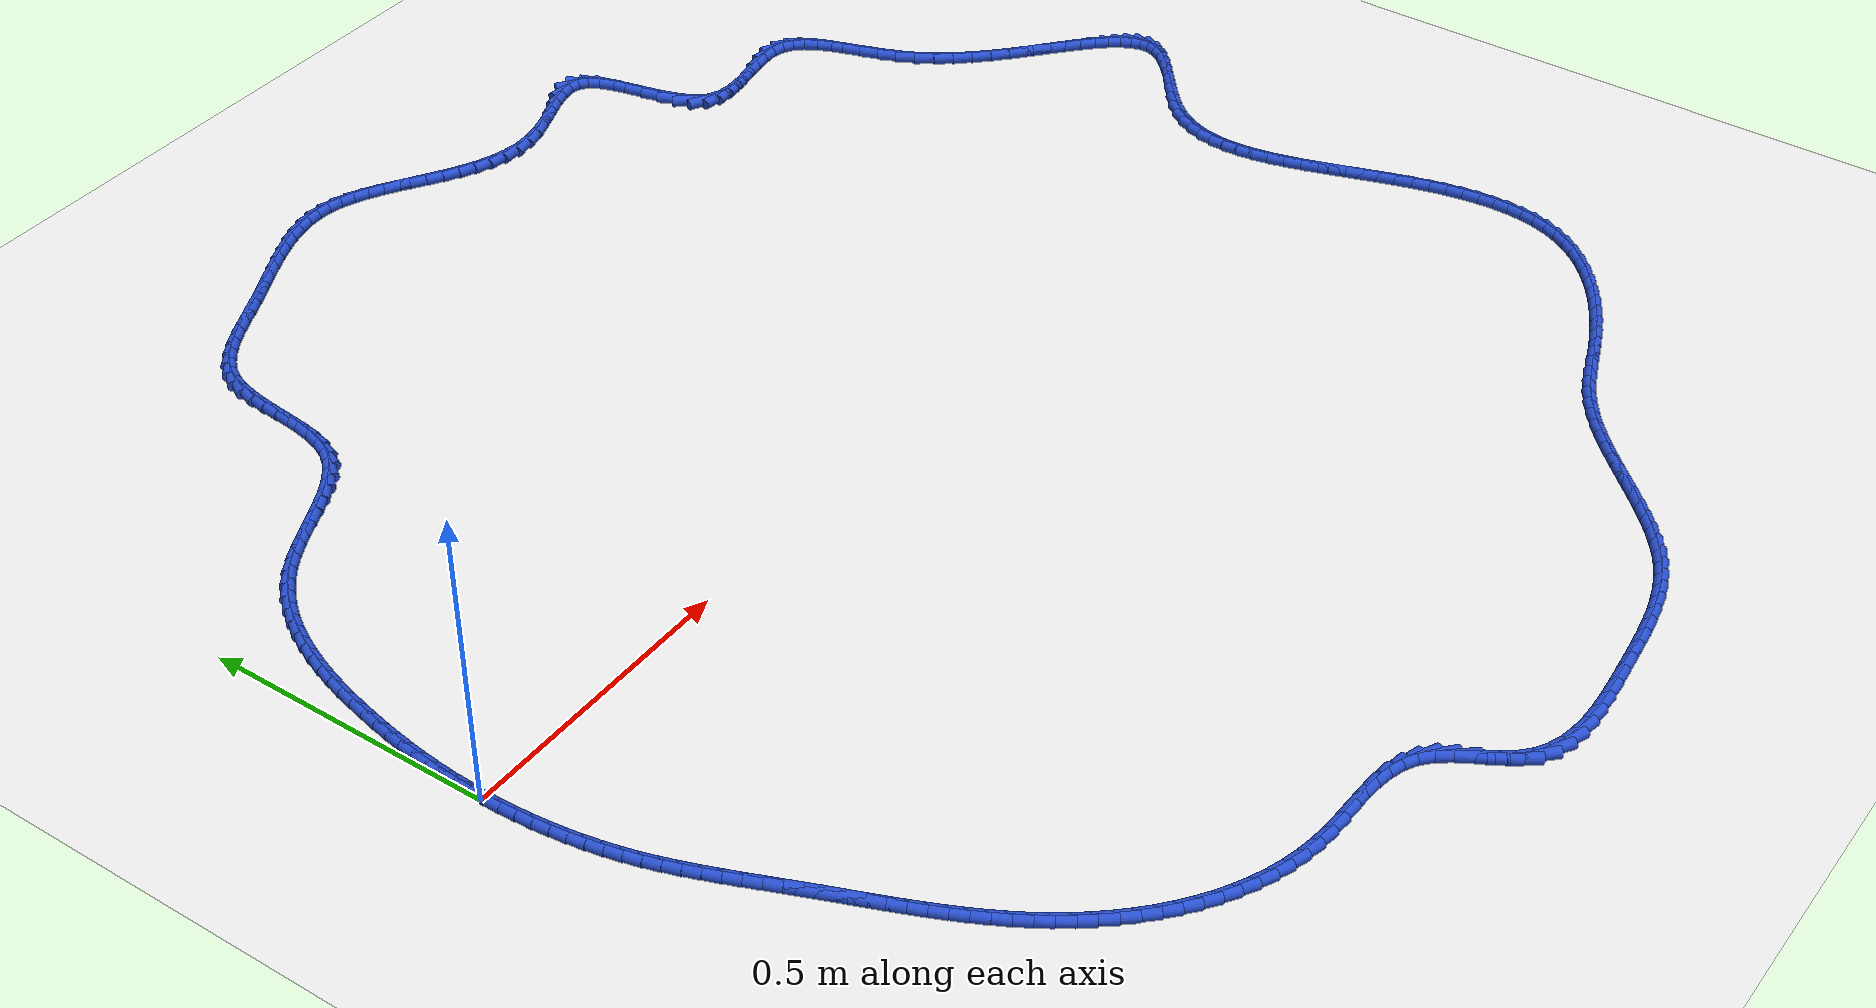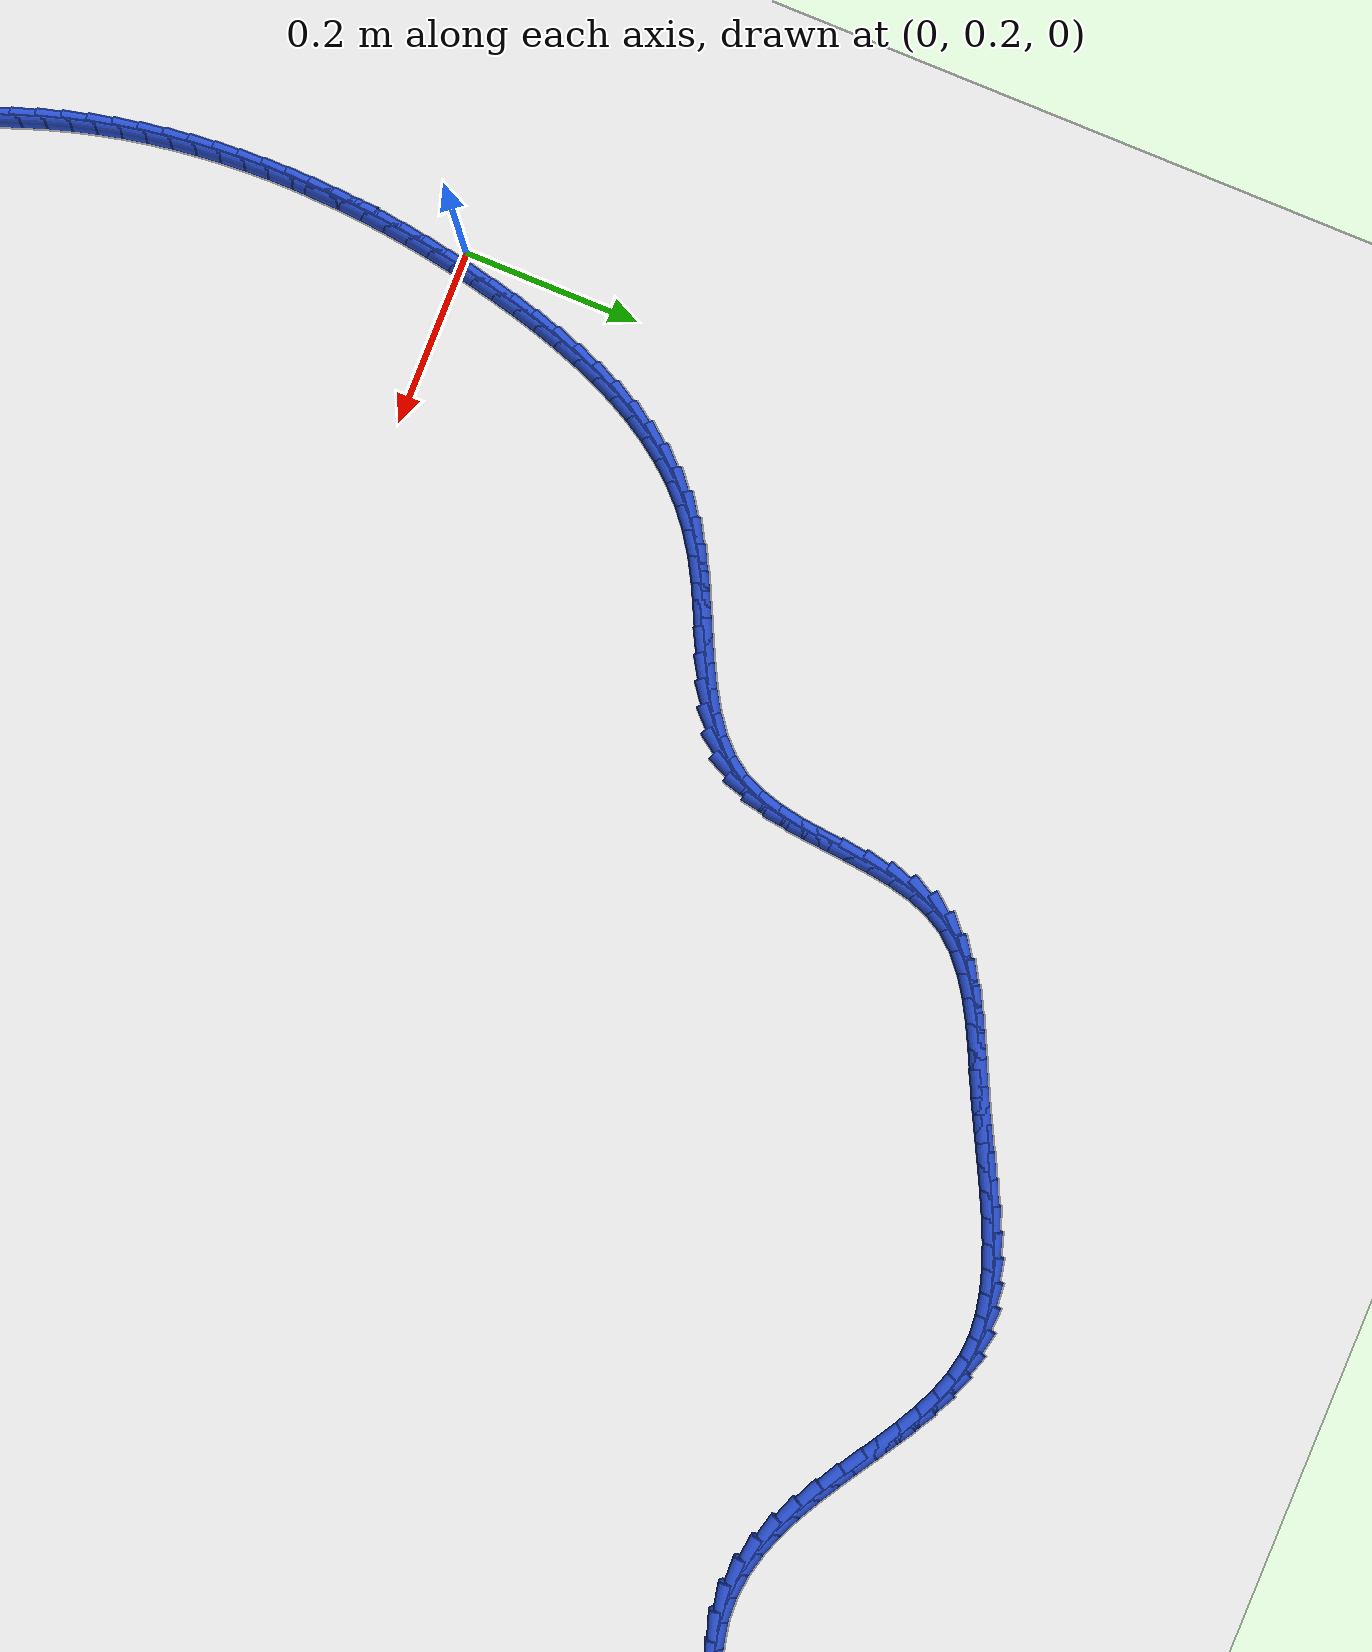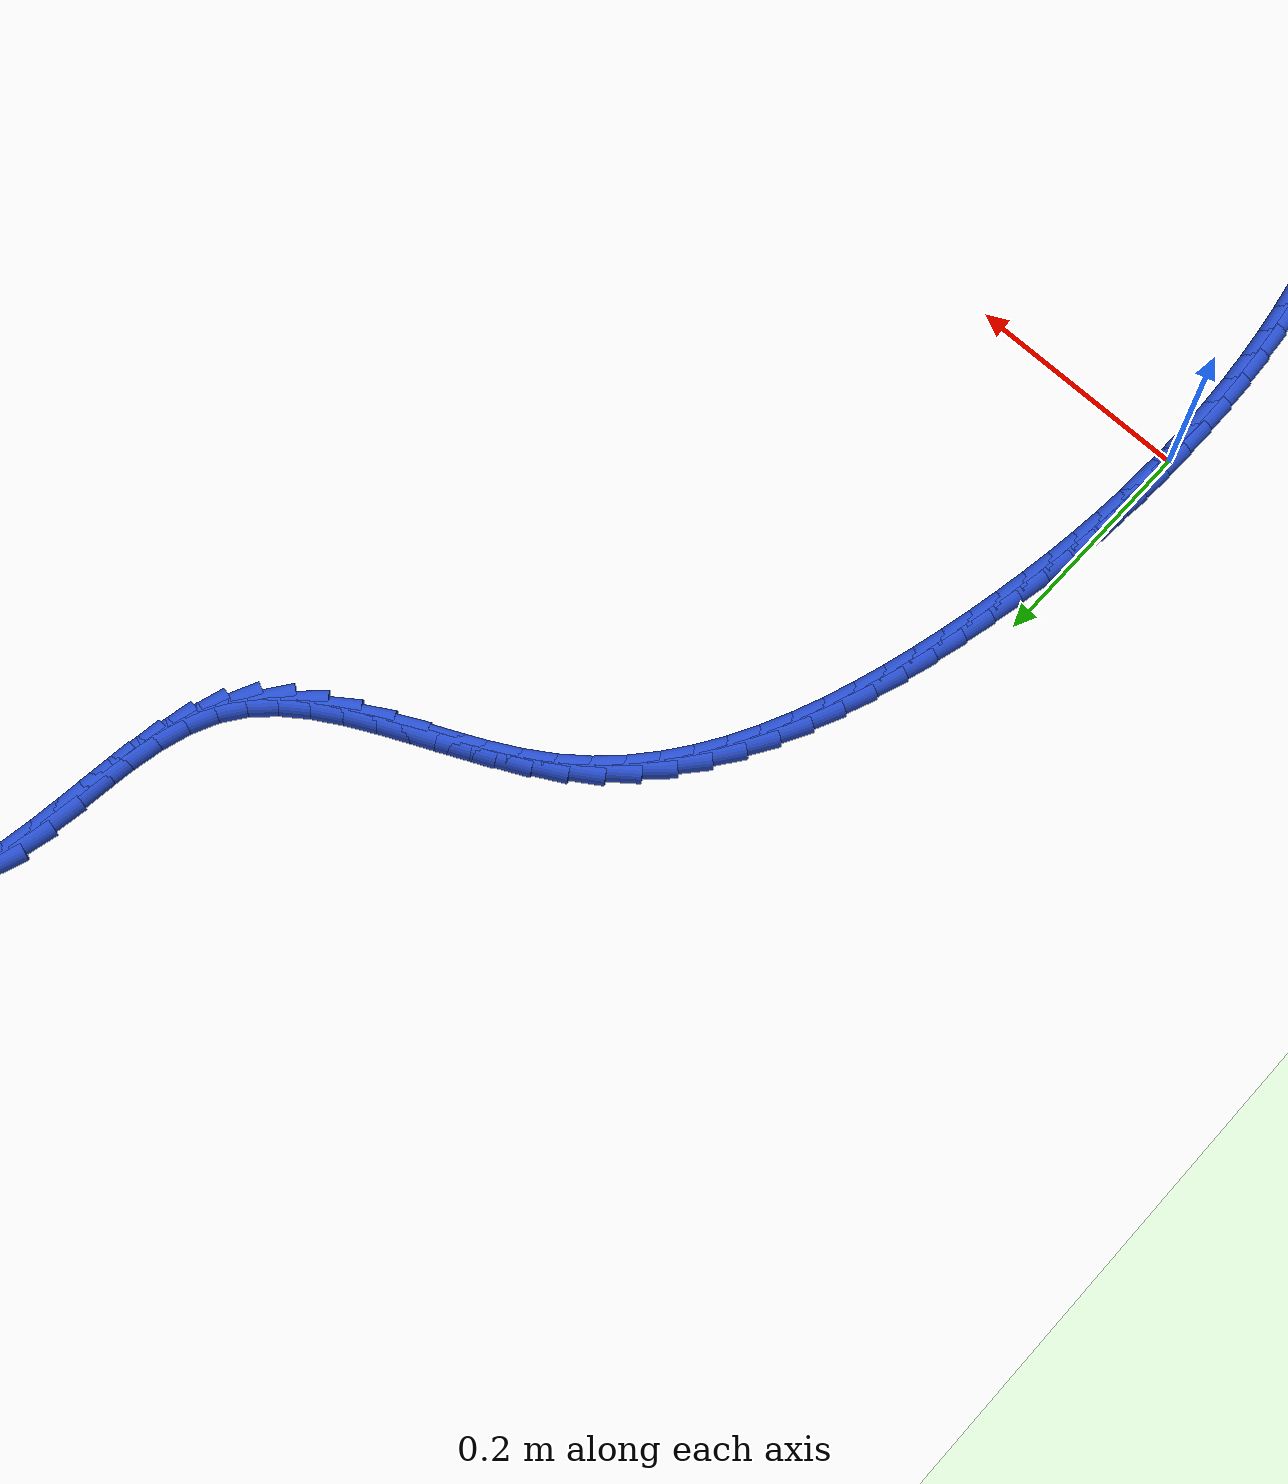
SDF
<sdf version="1.6">
 <world name="default">
  <light name="sun" type="directional">
   <pose>0 0 10 0 -0 0</pose>
   <diffuse>0.8 0.8 0.8 1</diffuse>
   <specular>0.2 0.2 0.2 1</specular>
   <attenuation>
    <range>1000</range>
    <constant>0.9</constant>
    <linear>0.01</linear>
    <quadratic>0.001</quadratic>
   </attenuation>
   <direction>-0.5 0.1 -0.9</direction>
  </light>
  <model name="ground_plane">
   <static>1</static>
   <link name="link">
    <collision name="collision">
     <geometry><plane><normal>0 0 1</normal><size>100 100</size></plane></geometry>
     <surface><friction><ode><mu>100</mu><mu2>50</mu2></ode></friction></surface>
    </collision>
    <visual name="visual">
     <cast_shadows>0</cast_shadows>
     <geometry><plane><normal>0 0 1</normal><size>100 100</size></plane></geometry>
     <material>
      <script><uri>file://media/materials/scripts/gazebo.material</uri><name>Gazebo/WhiteGlow</name></script>
     </material>
    </visual>
   </link>
  </model>
  <gravity>0 0 -9.8</gravity>
  <magnetic_field>6e-06 2.3e-05 -4.2e-05</magnetic_field>
  <atmosphere type="adiabatic"/>
  <physics name="default_physics" default="0" type="ode">
   <max_step_size>0.001</max_step_size>
   <real_time_factor>1</real_time_factor>
   <real_time_update_rate>1000</real_time_update_rate>
  </physics>
  <scene><ambient>0.4 0.4 0.4 1</ambient><background>0.7 0.7 0.7 1</background><shadows>1</shadows></scene>
  <spherical_coordinates>
   <surface_model>EARTH_WGS84</surface_model>
   <latitude_deg>0</latitude_deg>
   <longitude_deg>0</longitude_deg>
   <elevation>0</elevation>
   <heading_deg>0</heading_deg>
  </spherical_coordinates>
  <model name="line">
   <link name="link_0">
    <pose>1.1709383462843448e-17 -4.163336342344337e-17 0.01 0 1.57 1.5477169663119001</pose>
    <collision name="collision">
     <geometry><cylinder><radius>0.01</radius><length>0.08</length></cylinder></geometry>
    </collision>
    <visual name="visual">
     <material>
      <script><name>Gazebo/Blue</name><uri>file://media/materials/scripts/gazebo.material</uri></script>
     </material>
     <geometry><cylinder><radius>0.01</radius><length>0.08</length></cylinder></geometry>
    </visual>
   </link>
   <link name="link_1">
    <pose>0.0006372369864877311 0.027605783966620057 0.01 0 1.57 1.5208260116175845</pose>
    <collision name="collision">
     <geometry><cylinder><radius>0.01</radius><length>0.08</length></cylinder></geometry>
    </collision>
    <visual name="visual">
     <material>
      <script><name>Gazebo/Blue</name><uri>file://media/materials/scripts/gazebo.material</uri></script>
     </material>
     <geometry><cylinder><radius>0.01</radius><length>0.08</length></cylinder></geometry>
    </visual>
   </link>
   <link name="link_2">
    <pose>0.002013287063719354 0.055120209970029525 0.01 0 1.57 1.4944857000101304</pose>
    <collision name="collision">
     <geometry><cylinder><radius>0.01</radius><length>0.08</length></cylinder></geometry>
    </collision>
    <visual name="visual">
     <material>
      <script><name>Gazebo/Blue</name><uri>file://media/materials/scripts/gazebo.material</uri></script>
     </material>
     <geometry><cylinder><radius>0.01</radius><length>0.08</length></cylinder></geometry>
    </visual>
   </link>
   <link name="link_3">
    <pose>0.004112599532662749 0.08257688266017513 0.01 0 1.57 1.4688265475651985</pose>
    <collision name="collision">
     <geometry><cylinder><radius>0.01</radius><length>0.08</length></cylinder></geometry>
    </collision>
    <visual name="visual">
     <material>
      <script><name>Gazebo/Blue</name><uri>file://media/materials/scripts/gazebo.material</uri></script>
     </material>
     <geometry><cylinder><radius>0.01</radius><length>0.08</length></cylinder></geometry>
    </visual>
   </link>
   <link name="link_4">
    <pose>0.006919623694285787 0.11000940668700365 0.01 0 1.57 1.4439686259812823</pose>
    <collision name="collision">
     <geometry><cylinder><radius>0.01</radius><length>0.08</length></cylinder></geometry>
    </collision>
    <visual name="visual">
     <material>
      <script><name>Gazebo/Blue</name><uri>file://media/materials/scripts/gazebo.material</uri></script>
     </material>
     <geometry><cylinder><radius>0.01</radius><length>0.08</length></cylinder></geometry>
    </visual>
   </link>
   <link name="link_5">
    <pose>0.010418808849556344 0.137451386700462 0.01 0 1.57 1.4200196261016933</pose>
    <collision name="collision">
     <geometry><cylinder><radius>0.01</radius><length>0.08</length></cylinder></geometry>
    </collision>
    <visual name="visual">
     <material>
      <script><name>Gazebo/Blue</name><uri>file://media/materials/scripts/gazebo.material</uri></script>
     </material>
     <geometry><cylinder><radius>0.01</radius><length>0.08</length></cylinder></geometry>
    </visual>
   </link>
   <link name="link_6">
    <pose>0.014594604299442293 0.16493642735049693 0.01 0 1.57 1.3970734556359719</pose>
    <collision name="collision">
     <geometry><cylinder><radius>0.01</radius><length>0.08</length></cylinder></geometry>
    </collision>
    <visual name="visual">
     <material>
      <script><name>Gazebo/Blue</name><uri>file://media/materials/scripts/gazebo.material</uri></script>
     </material>
     <geometry><cylinder><radius>0.01</radius><length>0.08</length></cylinder></geometry>
    </visual>
   </link>
   <link name="link_7">
    <pose>0.01943145934491149 0.19249813328705517 0.01 0 1.57 1.375209386396989</pose>
    <collision name="collision">
     <geometry><cylinder><radius>0.01</radius><length>0.08</length></cylinder></geometry>
    </collision>
    <visual name="visual">
     <material>
      <script><name>Gazebo/Blue</name><uri>file://media/materials/scripts/gazebo.material</uri></script>
     </material>
     <geometry><cylinder><radius>0.01</radius><length>0.08</length></cylinder></geometry>
    </visual>
   </link>
   <link name="link_8">
    <pose>0.02491382328693183 0.2201701091600837 0.01 0 1.57 1.3544606109612891</pose>
    <collision name="collision">
     <geometry><cylinder><radius>0.01</radius><length>0.08</length></cylinder></geometry>
    </collision>
    <visual name="visual">
     <material>
      <script><name>Gazebo/Blue</name><uri>file://media/materials/scripts/gazebo.material</uri></script>
     </material>
     <geometry><cylinder><radius>0.01</radius><length>0.08</length></cylinder></geometry>
    </visual>
   </link>
   <link name="link_9">
    <pose>0.031026825061611793 0.2479849233616371 0.01 0 1.57 1.3326482929232633</pose>
    <collision name="collision">
     <geometry><cylinder><radius>0.01</radius><length>0.08</length></cylinder></geometry>
    </collision>
    <visual name="visual">
     <material>
      <script><name>Gazebo/Blue</name><uri>file://media/materials/scripts/gazebo.material</uri></script>
     </material>
     <geometry><cylinder><radius>0.01</radius><length>0.08</length></cylinder></geometry>
    </visual>
   </link>
   <link name="link_10">
    <pose>0.0378037564586045 0.2759017090916938 0.01 0 1.57 1.306014679405112</pose>
    <collision name="collision">
     <geometry><cylinder><radius>0.01</radius><length>0.08</length></cylinder></geometry>
    </collision>
    <visual name="visual">
     <material>
      <script><name>Gazebo/Blue</name><uri>file://media/materials/scripts/gazebo.material</uri></script>
     </material>
     <geometry><cylinder><radius>0.01</radius><length>0.08</length></cylinder></geometry>
    </visual>
   </link>
   <link name="link_11">
    <pose>0.04535714930381764 0.30375878014576996 0.01 0 1.57 1.2739533902682214</pose>
    <collision name="collision">
     <geometry><cylinder><radius>0.01</radius><length>0.08</length></cylinder></geometry>
    </collision>
    <visual name="visual">
     <material>
      <script><name>Gazebo/Blue</name><uri>file://media/materials/scripts/gazebo.material</uri></script>
     </material>
     <geometry><cylinder><radius>0.01</radius><length>0.08</length></cylinder></geometry>
    </visual>
   </link>
   <link name="link_12">
    <pose>0.05380691766932157 0.33138319441104125 0.01 0 1.57 1.2361039346219016</pose>
    <collision name="collision">
     <geometry><cylinder><radius>0.01</radius><length>0.08</length></cylinder></geometry>
    </collision>
    <visual name="visual">
     <material>
      <script><name>Gazebo/Blue</name><uri>file://media/materials/scripts/gazebo.material</uri></script>
     </material>
     <geometry><cylinder><radius>0.01</radius><length>0.08</length></cylinder></geometry>
    </visual>
   </link>
   <link name="link_13">
    <pose>0.06327297562718671 0.3586020097746833 0.01 0 1.57 1.1920336675245837</pose>
    <collision name="collision">
     <geometry><cylinder><radius>0.01</radius><length>0.08</length></cylinder></geometry>
    </collision>
    <visual name="visual">
     <material>
      <script><name>Gazebo/Blue</name><uri>file://media/materials/scripts/gazebo.material</uri></script>
     </material>
     <geometry><cylinder><radius>0.01</radius><length>0.08</length></cylinder></geometry>
    </visual>
   </link>
   <link name="link_14">
    <pose>0.07387523724948343 0.3852422841238716 0.01 0 1.57 1.1412676272345132</pose>
    <collision name="collision">
     <geometry><cylinder><radius>0.01</radius><length>0.08</length></cylinder></geometry>
    </collision>
    <visual name="visual">
     <material>
      <script><name>Gazebo/Blue</name><uri>file://media/materials/scripts/gazebo.material</uri></script>
     </material>
     <geometry><cylinder><radius>0.01</radius><length>0.08</length></cylinder></geometry>
    </visual>
   </link>
   <link name="link_15">
    <pose>0.08573361660828208 0.41113107534578175 0.01 0 1.57 1.0833346409436182</pose>
    <collision name="collision">
     <geometry><cylinder><radius>0.01</radius><length>0.08</length></cylinder></geometry>
    </collision>
    <visual name="visual">
     <material>
      <script><name>Gazebo/Blue</name><uri>file://media/materials/scripts/gazebo.material</uri></script>
     </material>
     <geometry><cylinder><radius>0.01</radius><length>0.08</length></cylinder></geometry>
    </visual>
   </link>
   <link name="link_16">
    <pose>0.09896802777565307 0.43609544132758954 0.01 0 1.57 1.0178364290178308</pose>
    <collision name="collision">
     <geometry><cylinder><radius>0.01</radius><length>0.08</length></cylinder></geometry>
    </collision>
    <visual name="visual">
     <material>
      <script><name>Gazebo/Blue</name><uri>file://media/materials/scripts/gazebo.material</uri></script>
     </material>
     <geometry><cylinder><radius>0.01</radius><length>0.08</length></cylinder></geometry>
    </visual>
   </link>
   <link name="link_17">
    <pose>0.11369838482366677 0.4599624399564705 0.01 0 1.57 0.9445443046762868</pose>
    <collision name="collision">
     <geometry><cylinder><radius>0.01</radius><length>0.08</length></cylinder></geometry>
    </collision>
    <visual name="visual">
     <material>
      <script><name>Gazebo/Blue</name><uri>file://media/materials/scripts/gazebo.material</uri></script>
     </material>
     <geometry><cylinder><radius>0.01</radius><length>0.08</length></cylinder></geometry>
    </visual>
   </link>
   <link name="link_18">
    <pose>0.1300446018243936 0.4825591291196002 0.01 0 1.57 0.8635213175206563</pose>
    <collision name="collision">
     <geometry><cylinder><radius>0.01</radius><length>0.08</length></cylinder></geometry>
    </collision>
    <visual name="visual">
     <material>
      <script><name>Gazebo/Blue</name><uri>file://media/materials/scripts/gazebo.material</uri></script>
     </material>
     <geometry><cylinder><radius>0.01</radius><length>0.08</length></cylinder></geometry>
    </visual>
   </link>
   <link name="link_19">
    <pose>0.14812659284990395 0.5037125667041544 0.01 0 1.57 0.7752544705329076</pose>
    <collision name="collision">
     <geometry><cylinder><radius>0.01</radius><length>0.08</length></cylinder></geometry>
    </collision>
    <visual name="visual">
     <material>
      <script><name>Gazebo/Blue</name><uri>file://media/materials/scripts/gazebo.material</uri></script>
     </material>
     <geometry><cylinder><radius>0.01</radius><length>0.08</length></cylinder></geometry>
    </visual>
   </link>
   <link name="link_20">
    <pose>0.16806427197226811 0.5232498105973087 0.01 0 1.57 0.6807633675997302</pose>
    <collision name="collision">
     <geometry><cylinder><radius>0.01</radius><length>0.08</length></cylinder></geometry>
    </collision>
    <visual name="visual">
     <material>
      <script><name>Gazebo/Blue</name><uri>file://media/materials/scripts/gazebo.material</uri></script>
     </material>
     <geometry><cylinder><radius>0.01</radius><length>0.08</length></cylinder></geometry>
    </visual>
   </link>
   <link name="link_21">
    <pose>0.18997755326355656 0.5409979186862386 0.01 0 1.57 0.5850759220808966</pose>
    <collision name="collision">
     <geometry><cylinder><radius>0.01</radius><length>0.08</length></cylinder></geometry>
    </collision>
    <visual name="visual">
     <material>
      <script><name>Gazebo/Blue</name><uri>file://media/materials/scripts/gazebo.material</uri></script>
     </material>
     <geometry><cylinder><radius>0.01</radius><length>0.08</length></cylinder></geometry>
    </visual>
   </link>
   <link name="link_22">
    <pose>0.21391069486639117 0.5568523675035043 0.01 0 1.57 0.5111507669095746</pose>
    <collision name="collision">
     <geometry><cylinder><radius>0.01</radius><length>0.08</length></cylinder></geometry>
    </collision>
    <visual name="visual">
     <material>
      <script><name>Gazebo/Blue</name><uri>file://media/materials/scripts/gazebo.material</uri></script>
     </material>
     <geometry><cylinder><radius>0.01</radius><length>0.08</length></cylinder></geometry>
    </visual>
   </link>
   <link name="link_23">
    <pose>0.2394132610267533 0.571156004812643 0.01 0 1.57 0.4655856947512719</pose>
    <collision name="collision">
     <geometry><cylinder><radius>0.01</radius><length>0.08</length></cylinder></geometry>
    </collision>
    <visual name="visual">
     <material>
      <script><name>Gazebo/Blue</name><uri>file://media/materials/scripts/gazebo.material</uri></script>
     </material>
     <geometry><cylinder><radius>0.01</radius><length>0.08</length></cylinder></geometry>
    </visual>
   </link>
   <link name="link_24">
    <pose>0.26583601929483264 0.5844314580816004 0.01 0 1.57 0.4462299824922771</pose>
    <collision name="collision">
     <geometry><cylinder><radius>0.01</radius><length>0.08</length></cylinder></geometry>
    </collision>
    <visual name="visual">
     <material>
      <script><name>Gazebo/Blue</name><uri>file://media/materials/scripts/gazebo.material</uri></script>
     </material>
     <geometry><cylinder><radius>0.01</radius><length>0.08</length></cylinder></geometry>
    </visual>
   </link>
   <link name="link_25">
    <pose>0.29252919797265386 0.5972018424417378 0.01 0 1.57 0.4523822597487026</pose>
    <collision name="collision">
     <geometry><cylinder><radius>0.01</radius><length>0.08</length></cylinder></geometry>
    </collision>
    <visual name="visual">
     <material>
      <script><name>Gazebo/Blue</name><uri>file://media/materials/scripts/gazebo.material</uri></script>
     </material>
     <geometry><cylinder><radius>0.01</radius><length>0.08</length></cylinder></geometry>
    </visual>
   </link>
   <link name="link_26">
    <pose>0.3188430253622414 0.6099902730244166 0.01 0 1.57 0.48515447964832475</pose>
    <collision name="collision">
     <geometry><cylinder><radius>0.01</radius><length>0.08</length></cylinder></geometry>
    </collision>
    <visual name="visual">
     <material>
      <script><name>Gazebo/Blue</name><uri>file://media/materials/scripts/gazebo.material</uri></script>
     </material>
     <geometry><cylinder><radius>0.01</radius><length>0.08</length></cylinder></geometry>
    </visual>
   </link>
   <link name="link_27">
    <pose>0.3441277297656195 0.6233198649609983 0.01 0 1.57 0.5475647684052095</pose>
    <collision name="collision">
     <geometry><cylinder><radius>0.01</radius><length>0.08</length></cylinder></geometry>
    </collision>
    <visual name="visual">
     <material>
      <script><name>Gazebo/Blue</name><uri>file://media/materials/scripts/gazebo.material</uri></script>
     </material>
     <geometry><cylinder><radius>0.01</radius><length>0.08</length></cylinder></geometry>
    </visual>
   </link>
   <link name="link_28">
    <pose>0.36773353948481313 0.6377137333828443 0.01 0 1.57 0.6442046673918681</pose>
    <collision name="collision">
     <geometry><cylinder><radius>0.01</radius><length>0.08</length></cylinder></geometry>
    </collision>
    <visual name="visual">
     <material>
      <script><name>Gazebo/Blue</name><uri>file://media/materials/scripts/gazebo.material</uri></script>
     </material>
     <geometry><cylinder><radius>0.01</radius><length>0.08</length></cylinder></geometry>
    </visual>
   </link>
   <link name="link_29">
    <pose>0.3890106828218462 0.6536949934213158 0.01 0 1.57 0.7797116133684148</pose>
    <collision name="collision">
     <geometry><cylinder><radius>0.01</radius><length>0.08</length></cylinder></geometry>
    </collision>
    <visual name="visual">
     <material>
      <script><name>Gazebo/Blue</name><uri>file://media/materials/scripts/gazebo.material</uri></script>
     </material>
     <geometry><cylinder><radius>0.01</radius><length>0.08</length></cylinder></geometry>
    </visual>
   </link>
   <link name="link_30">
    <pose>0.40730938807874373 0.6717867602077743 0.01 0 1.57 0.9548098722918194</pose>
    <collision name="collision">
     <geometry><cylinder><radius>0.01</radius><length>0.08</length></cylinder></geometry>
    </collision>
    <visual name="visual">
     <material>
      <script><name>Gazebo/Blue</name><uri>file://media/materials/scripts/gazebo.material</uri></script>
     </material>
     <geometry><cylinder><radius>0.01</radius><length>0.08</length></cylinder></geometry>
    </visual>
   </link>
   <link name="link_31">
    <pose>0.4219800958447993 0.6925119871100662 0.01 0 1.57 1.1447168873942477</pose>
    <collision name="collision">
     <geometry><cylinder><radius>0.01</radius><length>0.08</length></cylinder></geometry>
    </collision>
    <visual name="visual">
     <material>
      <script><name>Gazebo/Blue</name><uri>file://media/materials/scripts/gazebo.material</uri></script>
     </material>
     <geometry><cylinder><radius>0.01</radius><length>0.08</length></cylinder></geometry>
    </visual>
   </link>
   <link name="link_32">
    <pose>0.43270489422085223 0.7161409111302198 0.01 0 1.57 1.291662552783225</pose>
    <collision name="collision">
     <geometry><cylinder><radius>0.01</radius><length>0.08</length></cylinder></geometry>
    </collision>
    <visual name="visual">
     <material>
      <script><name>Gazebo/Blue</name><uri>file://media/materials/scripts/gazebo.material</uri></script>
     </material>
     <geometry><cylinder><radius>0.01</radius><length>0.08</length></cylinder></geometry>
    </visual>
   </link>
   <link name="link_33">
    <pose>0.44016814238733637 0.7421800358002898 0.01 0 1.57 1.3903196567529694</pose>
    <collision name="collision">
     <geometry><cylinder><radius>0.01</radius><length>0.08</length></cylinder></geometry>
    </collision>
    <visual name="visual">
     <material>
      <script><name>Gazebo/Blue</name><uri>file://media/materials/scripts/gazebo.material</uri></script>
     </material>
     <geometry><cylinder><radius>0.01</radius><length>0.08</length></cylinder></geometry>
    </visual>
   </link>
   <link name="link_34">
    <pose>0.44524279752796164 0.7699921524267631 0.01 0 1.57 1.4484645540056595</pose>
    <collision name="collision">
     <geometry><cylinder><radius>0.01</radius><length>0.08</length></cylinder></geometry>
    </collision>
    <visual name="visual">
     <material>
      <script><name>Gazebo/Blue</name><uri>file://media/materials/scripts/gazebo.material</uri></script>
     </material>
     <geometry><cylinder><radius>0.01</radius><length>0.08</length></cylinder></geometry>
    </visual>
   </link>
   <link name="link_35">
    <pose>0.4488018168264384 0.7989400523161267 0.01 0 1.57 1.4720795437632634</pose>
    <collision name="collision">
     <geometry><cylinder><radius>0.01</radius><length>0.08</length></cylinder></geometry>
    </collision>
    <visual name="visual">
     <material>
      <script><name>Gazebo/Blue</name><uri>file://media/materials/scripts/gazebo.material</uri></script>
     </material>
     <geometry><cylinder><radius>0.01</radius><length>0.08</length></cylinder></geometry>
    </visual>
   </link>
   <link name="link_36">
    <pose>0.4517181574664762 0.8283865267748662 0.01 0 1.57 1.4638416148519249</pose>
    <collision name="collision">
     <geometry><cylinder><radius>0.01</radius><length>0.08</length></cylinder></geometry>
    </collision>
    <visual name="visual">
     <material>
      <script><name>Gazebo/Blue</name><uri>file://media/materials/scripts/gazebo.material</uri></script>
     </material>
     <geometry><cylinder><radius>0.01</radius><length>0.08</length></cylinder></geometry>
    </visual>
   </link>
   <link name="link_37">
    <pose>0.4548647766317854 0.857694367109469 0.01 0 1.57 1.4229329572079816</pose>
    <collision name="collision">
     <geometry><cylinder><radius>0.01</radius><length>0.08</length></cylinder></geometry>
    </collision>
    <visual name="visual">
     <material>
      <script><name>Gazebo/Blue</name><uri>file://media/materials/scripts/gazebo.material</uri></script>
     </material>
     <geometry><cylinder><radius>0.01</radius><length>0.08</length></cylinder></geometry>
    </visual>
   </link>
   <link name="link_38">
    <pose>0.45911463150607573 0.8862263646264211 0.01 0 1.57 1.3451240663873456</pose>
    <collision name="collision">
     <geometry><cylinder><radius>0.01</radius><length>0.08</length></cylinder></geometry>
    </collision>
    <visual name="visual">
     <material>
      <script><name>Gazebo/Blue</name><uri>file://media/materials/scripts/gazebo.material</uri></script>
     </material>
     <geometry><cylinder><radius>0.01</radius><length>0.08</length></cylinder></geometry>
    </visual>
   </link>
   <link name="link_39">
    <pose>0.4653406792730572 0.9133453106322095 0.01 0 1.57 1.2234595726392983</pose>
    <collision name="collision">
     <geometry><cylinder><radius>0.01</radius><length>0.08</length></cylinder></geometry>
    </collision>
    <visual name="visual">
     <material>
      <script><name>Gazebo/Blue</name><uri>file://media/materials/scripts/gazebo.material</uri></script>
     </material>
     <geometry><cylinder><radius>0.01</radius><length>0.08</length></cylinder></geometry>
    </visual>
   </link>
   <link name="link_40">
    <pose>0.47441587711644007 0.9384139964333205 0.01 0 1.57 1.0526101060902298</pose>
    <collision name="collision">
     <geometry><cylinder><radius>0.01</radius><length>0.08</length></cylinder></geometry>
    </collision>
    <visual name="visual">
     <material>
      <script><name>Gazebo/Blue</name><uri>file://media/materials/scripts/gazebo.material</uri></script>
     </material>
     <geometry><cylinder><radius>0.01</radius><length>0.08</length></cylinder></geometry>
    </visual>
   </link>
   <link name="link_41">
    <pose>0.4871878280152746 0.9608147994104809 0.01 0 1.57 0.8678882118703893</pose>
    <collision name="collision">
     <geometry><cylinder><radius>0.01</radius><length>0.08</length></cylinder></geometry>
    </collision>
    <visual name="visual">
     <material>
      <script><name>Gazebo/Blue</name><uri>file://media/materials/scripts/gazebo.material</uri></script>
     </material>
     <geometry><cylinder><radius>0.01</radius><length>0.08</length></cylinder></geometry>
    </visual>
   </link>
   <link name="link_42">
    <pose>0.5038269260415796 0.9804532395200742 0.01 0 1.57 0.7159484637429826</pose>
    <collision name="collision">
     <geometry><cylinder><radius>0.01</radius><length>0.08</length></cylinder></geometry>
    </collision>
    <visual name="visual">
     <material>
      <script><name>Gazebo/Blue</name><uri>file://media/materials/scripts/gazebo.material</uri></script>
     </material>
     <geometry><cylinder><radius>0.01</radius><length>0.08</length></cylinder></geometry>
    </visual>
   </link>
   <link name="link_43">
    <pose>0.5237695707246781 0.997801846088262 0.01 0 1.57 0.6020070279841664</pose>
    <collision name="collision">
     <geometry><cylinder><radius>0.01</radius><length>0.08</length></cylinder></geometry>
    </collision>
    <visual name="visual">
     <material>
      <script><name>Gazebo/Blue</name><uri>file://media/materials/scripts/gazebo.material</uri></script>
     </material>
     <geometry><cylinder><radius>0.01</radius><length>0.08</length></cylinder></geometry>
    </visual>
   </link>
   <link name="link_44">
    <pose>0.546415427173407 1.01336152571024 0.01 0 1.57 0.5230825780058246</pose>
    <collision name="collision">
     <geometry><cylinder><radius>0.01</radius><length>0.08</length></cylinder></geometry>
    </collision>
    <visual name="visual">
     <material>
      <script><name>Gazebo/Blue</name><uri>file://media/materials/scripts/gazebo.material</uri></script>
     </material>
     <geometry><cylinder><radius>0.01</radius><length>0.08</length></cylinder></geometry>
    </visual>
   </link>
   <link name="link_45">
    <pose>0.5711641604966038 1.0276331849812053 0.01 0 1.57 0.4745253025807204</pose>
    <collision name="collision">
     <geometry><cylinder><radius>0.01</radius><length>0.08</length></cylinder></geometry>
    </collision>
    <visual name="visual">
     <material>
      <script><name>Gazebo/Blue</name><uri>file://media/materials/scripts/gazebo.material</uri></script>
     </material>
     <geometry><cylinder><radius>0.01</radius><length>0.08</length></cylinder></geometry>
    </visual>
   </link>
   <link name="link_46">
    <pose>0.5974154358031061 1.041117730496354 0.01 0 1.57 0.45243702331978924</pose>
    <collision name="collision">
     <geometry><cylinder><radius>0.01</radius><length>0.08</length></cylinder></geometry>
    </collision>
    <visual name="visual">
     <material>
      <script><name>Gazebo/Blue</name><uri>file://media/materials/scripts/gazebo.material</uri></script>
     </material>
     <geometry><cylinder><radius>0.01</radius><length>0.08</length></cylinder></geometry>
    </visual>
   </link>
   <link name="link_47">
    <pose>0.624568918201751 1.054316068850883 0.01 0 1.57 0.4544303903207774</pose>
    <collision name="collision">
     <geometry><cylinder><radius>0.01</radius><length>0.08</length></cylinder></geometry>
    </collision>
    <visual name="visual">
     <material>
      <script><name>Gazebo/Blue</name><uri>file://media/materials/scripts/gazebo.material</uri></script>
     </material>
     <geometry><cylinder><radius>0.01</radius><length>0.08</length></cylinder></geometry>
    </visual>
   </link>
   <link name="link_48">
    <pose>0.6520243897971952 1.067728918063453 0.01 0 1.57 0.4714313010147207</pose>
    <collision name="collision">
     <geometry><cylinder><radius>0.01</radius><length>0.08</length></cylinder></geometry>
    </collision>
    <visual name="visual">
     <material>
      <script><name>Gazebo/Blue</name><uri>file://media/materials/scripts/gazebo.material</uri></script>
     </material>
     <geometry><cylinder><radius>0.01</radius><length>0.08</length></cylinder></geometry>
    </visual>
   </link>
   <link name="link_49">
    <pose>0.6793155837851782 1.0816410907233474 0.01 0 1.57 0.47945931707030587</pose>
    <collision name="collision">
     <geometry><cylinder><radius>0.01</radius><length>0.08</length></cylinder></geometry>
    </collision>
    <visual name="visual">
     <material>
      <script><name>Gazebo/Blue</name><uri>file://media/materials/scripts/gazebo.material</uri></script>
     </material>
     <geometry><cylinder><radius>0.01</radius><length>0.08</length></cylinder></geometry>
    </visual>
   </link>
   <link name="link_50">
    <pose>0.7063678381431344 1.0957062018845758 0.01 0 1.57 0.474096318448564</pose>
    <collision name="collision">
     <geometry><cylinder><radius>0.01</radius><length>0.08</length></cylinder></geometry>
    </collision>
    <visual name="visual">
     <material>
      <script><name>Gazebo/Blue</name><uri>file://media/materials/scripts/gazebo.material</uri></script>
     </material>
     <geometry><cylinder><radius>0.01</radius><length>0.08</length></cylinder></geometry>
    </visual>
   </link>
   <link name="link_51">
    <pose>0.733177674037686 1.1094631319102832 0.01 0 1.57 0.45474403150399456</pose>
    <collision name="collision">
     <geometry><cylinder><radius>0.01</radius><length>0.08</length></cylinder></geometry>
    </collision>
    <visual name="visual">
     <material>
      <script><name>Gazebo/Blue</name><uri>file://media/materials/scripts/gazebo.material</uri></script>
     </material>
     <geometry><cylinder><radius>0.01</radius><length>0.08</length></cylinder></geometry>
    </visual>
   </link>
   <link name="link_52">
    <pose>0.7597416126354554 1.1224507611636152 0.01 0 1.57 0.4201852582547956</pose>
    <collision name="collision">
     <geometry><cylinder><radius>0.01</radius><length>0.08</length></cylinder></geometry>
    </collision>
    <visual name="visual">
     <material>
      <script><name>Gazebo/Blue</name><uri>file://media/materials/scripts/gazebo.material</uri></script>
     </material>
     <geometry><cylinder><radius>0.01</radius><length>0.08</length></cylinder></geometry>
    </visual>
   </link>
   <link name="link_53">
    <pose>0.7860561751030654 1.134207970007717 0.01 0 1.57 0.36857479426464224</pose>
    <collision name="collision">
     <geometry><cylinder><radius>0.01</radius><length>0.08</length></cylinder></geometry>
    </collision>
    <visual name="visual">
     <material>
      <script><name>Gazebo/Blue</name><uri>file://media/materials/scripts/gazebo.material</uri></script>
     </material>
     <geometry><cylinder><radius>0.01</radius><length>0.08</length></cylinder></geometry>
    </visual>
   </link>
   <link name="link_54">
    <pose>0.812117882607139 1.1442736388057342 0.01 0 1.57 0.2975390971836306</pose>
    <collision name="collision">
     <geometry><cylinder><radius>0.01</radius><length>0.08</length></cylinder></geometry>
    </collision>
    <visual name="visual">
     <material>
      <script><name>Gazebo/Blue</name><uri>file://media/materials/scripts/gazebo.material</uri></script>
     </material>
     <geometry><cylinder><radius>0.01</radius><length>0.08</length></cylinder></geometry>
    </visual>
   </link>
   <link name="link_55">
    <pose>0.8379232563142981 1.1521866479208116 0.01 0 1.57 0.2045412631188753</pose>
    <collision name="collision">
     <geometry><cylinder><radius>0.01</radius><length>0.08</length></cylinder></geometry>
    </collision>
    <visual name="visual">
     <material>
      <script><name>Gazebo/Blue</name><uri>file://media/materials/scripts/gazebo.material</uri></script>
     </material>
     <geometry><cylinder><radius>0.01</radius><length>0.08</length></cylinder></geometry>
    </visual>
   </link>
   <link name="link_56">
    <pose>0.8634688173911657 1.157485877716095 0.01 0 1.57 0.08775391873776302</pose>
    <collision name="collision">
     <geometry><cylinder><radius>0.01</radius><length>0.08</length></cylinder></geometry>
    </collision>
    <visual name="visual">
     <material>
      <script><name>Gazebo/Blue</name><uri>file://media/materials/scripts/gazebo.material</uri></script>
     </material>
     <geometry><cylinder><radius>0.01</radius><length>0.08</length></cylinder></geometry>
    </visual>
   </link>
   <link name="link_57">
    <pose>0.888751087004364 1.15971020855473 0.01 0 1.57 -0.052386787738391</pose>
    <collision name="collision">
     <geometry><cylinder><radius>0.01</radius><length>0.08</length></cylinder></geometry>
    </collision>
    <visual name="visual">
     <material>
      <script><name>Gazebo/Blue</name><uri>file://media/materials/scripts/gazebo.material</uri></script>
     </material>
     <geometry><cylinder><radius>0.01</radius><length>0.08</length></cylinder></geometry>
    </visual>
   </link>
   <link name="link_58">
    <pose>0.9137665868100378 1.158398526740824 0.01 0 1.57 -0.20344666515201165</pose>
    <collision name="collision">
     <geometry><cylinder><radius>0.01</radius><length>0.08</length></cylinder></geometry>
    </collision>
    <visual name="visual">
     <material>
      <script><name>Gazebo/Blue</name><uri>file://media/materials/scripts/gazebo.material</uri></script>
     </material>
     <geometry><cylinder><radius>0.01</radius><length>0.08</length></cylinder></geometry>
    </visual>
   </link>
   <link name="link_59">
    <pose>0.938528353803507 1.1532901531169648 0.01 0 1.57 -0.3306382047764136</pose>
    <collision name="collision">
     <geometry><cylinder><radius>0.01</radius><length>0.08</length></cylinder></geometry>
    </collision>
    <visual name="visual">
     <material>
      <script><name>Gazebo/Blue</name><uri>file://media/materials/scripts/gazebo.material</uri></script>
     </material>
     <geometry><cylinder><radius>0.01</radius><length>0.08</length></cylinder></geometry>
    </visual>
   </link>
   <link name="link_60">
    <pose>0.9631094577050308 1.144852981604869 0.01 0 1.57 -0.42669723053227326</pose>
    <collision name="collision">
     <geometry><cylinder><radius>0.01</radius><length>0.08</length></cylinder></geometry>
    </collision>
    <visual name="visual">
     <material>
      <script><name>Gazebo/Blue</name><uri>file://media/materials/scripts/gazebo.material</uri></script>
     </material>
     <geometry><cylinder><radius>0.01</radius><length>0.08</length></cylinder></geometry>
    </visual>
   </link>
   <link name="link_61">
    <pose>0.9875966045251326 1.1337203997632013 0.01 0 1.57 -0.494356832496948</pose>
    <collision name="collision">
     <geometry><cylinder><radius>0.01</radius><length>0.08</length></cylinder></geometry>
    </collision>
    <visual name="visual">
     <material>
      <script><name>Gazebo/Blue</name><uri>file://media/materials/scripts/gazebo.material</uri></script>
     </material>
     <geometry><cylinder><radius>0.01</radius><length>0.08</length></cylinder></geometry>
    </visual>
   </link>
   <link name="link_62">
    <pose>1.0120765002743368 1.1205257951506256 0.01 0 1.57 -0.5370483914675811</pose>
    <collision name="collision">
     <geometry><cylinder><radius>0.01</radius><length>0.08</length></cylinder></geometry>
    </collision>
    <visual name="visual">
     <material>
      <script><name>Gazebo/Blue</name><uri>file://media/materials/scripts/gazebo.material</uri></script>
     </material>
     <geometry><cylinder><radius>0.01</radius><length>0.08</length></cylinder></geometry>
    </visual>
   </link>
   <link name="link_63">
    <pose>1.0366358509631661 1.1059025553258064 0.01 0 1.57 -0.5575819934053063</pose>
    <collision name="collision">
     <geometry><cylinder><radius>0.01</radius><length>0.08</length></cylinder></geometry>
    </collision>
    <visual name="visual">
     <material>
      <script><name>Gazebo/Blue</name><uri>file://media/materials/scripts/gazebo.material</uri></script>
     </material>
     <geometry><cylinder><radius>0.01</radius><length>0.08</length></cylinder></geometry>
    </visual>
   </link>
   <link name="link_64">
    <pose>1.0613613626021448 1.0904840678474084 0.01 0 1.57 -0.5577023526416753</pose>
    <collision name="collision">
     <geometry><cylinder><radius>0.01</radius><length>0.08</length></cylinder></geometry>
    </collision>
    <visual name="visual">
     <material>
      <script><name>Gazebo/Blue</name><uri>file://media/materials/scripts/gazebo.material</uri></script>
     </material>
     <geometry><cylinder><radius>0.01</radius><length>0.08</length></cylinder></geometry>
    </visual>
   </link>
   <link name="link_65">
    <pose>1.0863397412017957 1.0749037202740948 0.01 0 1.57 -0.5380360521402066</pose>
    <collision name="collision">
     <geometry><cylinder><radius>0.01</radius><length>0.08</length></cylinder></geometry>
    </collision>
    <visual name="visual">
     <material>
      <script><name>Gazebo/Blue</name><uri>file://media/materials/scripts/gazebo.material</uri></script>
     </material>
     <geometry><cylinder><radius>0.01</radius><length>0.08</length></cylinder></geometry>
    </visual>
   </link>
   <link name="link_66">
    <pose>1.1116576927726431 1.059794900164531 0.01 0 1.57 -0.4981963521127707</pose>
    <collision name="collision">
     <geometry><cylinder><radius>0.01</radius><length>0.08</length></cylinder></geometry>
    </collision>
    <visual name="visual">
     <material>
      <script><name>Gazebo/Blue</name><uri>file://media/materials/scripts/gazebo.material</uri></script>
     </material>
     <geometry><cylinder><radius>0.01</radius><length>0.08</length></cylinder></geometry>
    </visual>
   </link>
   <link name="link_67">
    <pose>1.1374019233252106 1.0457909950773805 0.01 0 1.57 -0.4370097366161705</pose>
    <collision name="collision">
     <geometry><cylinder><radius>0.01</radius><length>0.08</length></cylinder></geometry>
    </collision>
    <visual name="visual">
     <material>
      <script><name>Gazebo/Blue</name><uri>file://media/materials/scripts/gazebo.material</uri></script>
     </material>
     <geometry><cylinder><radius>0.01</radius><length>0.08</length></cylinder></geometry>
    </visual>
   </link>
   <link name="link_68">
    <pose>1.1636591388700213 1.033525392571308 0.01 0 1.57 -0.35296621191783484</pose>
    <collision name="collision">
     <geometry><cylinder><radius>0.01</radius><length>0.08</length></cylinder></geometry>
    </collision>
    <visual name="visual">
     <material>
      <script><name>Gazebo/Blue</name><uri>file://media/materials/scripts/gazebo.material</uri></script>
     </material>
     <geometry><cylinder><radius>0.01</radius><length>0.08</length></cylinder></geometry>
    </visual>
   </link>
   <link name="link_69">
    <pose>1.1905160454175991 1.0236314802049775 0.01 0 1.57 -0.24508147279829431</pose>
    <collision name="collision">
     <geometry><cylinder><radius>0.01</radius><length>0.08</length></cylinder></geometry>
    </collision>
    <visual name="visual">
     <material>
      <script><name>Gazebo/Blue</name><uri>file://media/materials/scripts/gazebo.material</uri></script>
     </material>
     <geometry><cylinder><radius>0.01</radius><length>0.08</length></cylinder></geometry>
    </visual>
   </link>
   <link name="link_70">
    <pose>1.2180593489784677 1.0167426455370534 0.01 0 1.57 -0.11428729150965329</pose>
    <collision name="collision">
     <geometry><cylinder><radius>0.01</radius><length>0.08</length></cylinder></geometry>
    </collision>
    <visual name="visual">
     <material>
      <script><name>Gazebo/Blue</name><uri>file://media/materials/scripts/gazebo.material</uri></script>
     </material>
     <geometry><cylinder><radius>0.01</radius><length>0.08</length></cylinder></geometry>
    </visual>
   </link>
   <link name="link_71">
    <pose>1.2463757555631507 1.0134922761262006 0.01 0 1.57 0.034996531459187845</pose>
    <collision name="collision">
     <geometry><cylinder><radius>0.01</radius><length>0.08</length></cylinder></geometry>
    </collision>
    <visual name="visual">
     <material>
      <script><name>Gazebo/Blue</name><uri>file://media/materials/scripts/gazebo.material</uri></script>
     </material>
     <geometry><cylinder><radius>0.01</radius><length>0.08</length></cylinder></geometry>
    </visual>
   </link>
   <link name="link_72">
    <pose>1.2755519711821708 1.0145137595310822 0.01 0 1.57 0.19273076693864225</pose>
    <collision name="collision">
     <geometry><cylinder><radius>0.01</radius><length>0.08</length></cylinder></geometry>
    </collision>
    <visual name="visual">
     <material>
      <script><name>Gazebo/Blue</name><uri>file://media/materials/scripts/gazebo.material</uri></script>
     </material>
     <geometry><cylinder><radius>0.01</radius><length>0.08</length></cylinder></geometry>
    </visual>
   </link>
   <link name="link_73">
    <pose>1.3056576645841445 1.0203889789914729 0.01 0 1.57 0.3146425083497597</pose>
    <collision name="collision">
     <geometry><cylinder><radius>0.01</radius><length>0.08</length></cylinder></geometry>
    </collision>
    <visual name="visual">
     <material>
      <script><name>Gazebo/Blue</name><uri>file://media/materials/scripts/gazebo.material</uri></script>
     </material>
     <geometry><cylinder><radius>0.01</radius><length>0.08</length></cylinder></geometry>
    </visual>
   </link>
   <link name="link_74">
    <pose>1.3363222430851602 1.0303688899644101 0.01 0 1.57 0.3738013823674872</pose>
    <collision name="collision">
     <geometry><cylinder><radius>0.01</radius><length>0.08</length></cylinder></geometry>
    </collision>
    <visual name="visual">
     <material>
      <script><name>Gazebo/Blue</name><uri>file://media/materials/scripts/gazebo.material</uri></script>
     </material>
     <geometry><cylinder><radius>0.01</radius><length>0.08</length></cylinder></geometry>
    </visual>
   </link>
   <link name="link_75">
    <pose>1.3667061539668321 1.0422867631115629 0.01 0 1.57 0.37825981146786636</pose>
    <collision name="collision">
     <geometry><cylinder><radius>0.01</radius><length>0.08</length></cylinder></geometry>
    </collision>
    <visual name="visual">
     <material>
      <script><name>Gazebo/Blue</name><uri>file://media/materials/scripts/gazebo.material</uri></script>
     </material>
     <geometry><cylinder><radius>0.01</radius><length>0.08</length></cylinder></geometry>
    </visual>
   </link>
   <link name="link_76">
    <pose>1.395947060352348 1.0539069916794725 0.01 0 1.57 0.3220299427260602</pose>
    <collision name="collision">
     <geometry><cylinder><radius>0.01</radius><length>0.08</length></cylinder></geometry>
    </collision>
    <visual name="visual">
     <material>
      <script><name>Gazebo/Blue</name><uri>file://media/materials/scripts/gazebo.material</uri></script>
     </material>
     <geometry><cylinder><radius>0.01</radius><length>0.08</length></cylinder></geometry>
    </visual>
   </link>
   <link name="link_77">
    <pose>1.423182625364898 1.062993968914682 0.01 0 1.57 0.17538465028722955</pose>
    <collision name="collision">
     <geometry><cylinder><radius>0.01</radius><length>0.08</length></cylinder></geometry>
    </collision>
    <visual name="visual">
     <material>
      <script><name>Gazebo/Blue</name><uri>file://media/materials/scripts/gazebo.material</uri></script>
     </material>
     <geometry><cylinder><radius>0.01</radius><length>0.08</length></cylinder></geometry>
    </visual>
   </link>
   <link name="link_78">
    <pose>1.447550512127672 1.0673120880637341 0.01 0 1.57 -0.12943807461948464</pose>
    <collision name="collision">
     <geometry><cylinder><radius>0.01</radius><length>0.08</length></cylinder></geometry>
    </collision>
    <visual name="visual">
     <material>
      <script><name>Gazebo/Blue</name><uri>file://media/materials/scripts/gazebo.material</uri></script>
     </material>
     <geometry><cylinder><radius>0.01</radius><length>0.08</length></cylinder></geometry>
    </visual>
   </link>
   <link name="link_79">
    <pose>1.4681883837638576 1.0646257423731702 0.01 0 1.57 -0.6248769603486185</pose>
    <collision name="collision">
     <geometry><cylinder><radius>0.01</radius><length>0.08</length></cylinder></geometry>
    </collision>
    <visual name="visual">
     <material>
      <script><name>Gazebo/Blue</name><uri>file://media/materials/scripts/gazebo.material</uri></script>
     </material>
     <geometry><cylinder><radius>0.01</radius><length>0.08</length></cylinder></geometry>
    </visual>
   </link>
   <link name="link_80">
    <pose>1.4843564554706972 1.052963754758348 0.01 0 1.57 -1.024371086084633</pose>
    <collision name="collision">
     <geometry><cylinder><radius>0.01</radius><length>0.08</length></cylinder></geometry>
    </collision>
    <visual name="visual">
     <material>
      <script><name>Gazebo/Blue</name><uri>file://media/materials/scripts/gazebo.material</uri></script>
     </material>
     <geometry><cylinder><radius>0.01</radius><length>0.08</length></cylinder></geometry>
    </visual>
   </link>
   <link name="link_81">
    <pose>1.4965224535259907 1.0329603855178144 0.01 0 1.57 -1.2294171807697014</pose>
    <collision name="collision">
     <geometry><cylinder><radius>0.01</radius><length>0.08</length></cylinder></geometry>
    </collision>
    <visual name="visual">
     <material>
      <script><name>Gazebo/Blue</name><uri>file://media/materials/scripts/gazebo.material</uri></script>
     </material>
     <geometry><cylinder><radius>0.01</radius><length>0.08</length></cylinder></geometry>
    </visual>
   </link>
   <link name="link_82">
    <pose>1.5058410668014626 1.006732148862219 0.01 0 1.57 -1.3241421969394336</pose>
    <collision name="collision">
     <geometry><cylinder><radius>0.01</radius><length>0.08</length></cylinder></geometry>
    </collision>
    <visual name="visual">
     <material>
      <script><name>Gazebo/Blue</name><uri>file://media/materials/scripts/gazebo.material</uri></script>
     </material>
     <geometry><cylinder><radius>0.01</radius><length>0.08</length></cylinder></geometry>
    </visual>
   </link>
   <link name="link_83">
    <pose>1.5134749267230345 0.9764126965903895 0.01 0 1.57 -1.353927051850173</pose>
    <collision name="collision">
     <geometry><cylinder><radius>0.01</radius><length>0.08</length></cylinder></geometry>
    </collision>
    <visual name="visual">
     <material>
      <script><name>Gazebo/Blue</name><uri>file://media/materials/scripts/gazebo.material</uri></script>
     </material>
     <geometry><cylinder><radius>0.01</radius><length>0.08</length></cylinder></geometry>
    </visual>
   </link>
   <link name="link_84">
    <pose>1.5205866647166275 0.9441356805011556 0.01 0 1.57 -1.3338372518909762</pose>
    <collision name="collision">
     <geometry><cylinder><radius>0.01</radius><length>0.08</length></cylinder></geometry>
    </collision>
    <visual name="visual">
     <material>
      <script><name>Gazebo/Blue</name><uri>file://media/materials/scripts/gazebo.material</uri></script>
     </material>
     <geometry><cylinder><radius>0.01</radius><length>0.08</length></cylinder></geometry>
    </visual>
   </link>
   <link name="link_85">
    <pose>1.5283389122081614 0.9120347523933439 0.01 0 1.57 -1.2604173127748963</pose>
    <collision name="collision">
     <geometry><cylinder><radius>0.01</radius><length>0.08</length></cylinder></geometry>
    </collision>
    <visual name="visual">
     <material>
      <script><name>Gazebo/Blue</name><uri>file://media/materials/scripts/gazebo.material</uri></script>
     </material>
     <geometry><cylinder><radius>0.01</radius><length>0.08</length></cylinder></geometry>
    </visual>
   </link>
   <link name="link_86">
    <pose>1.5378943006235577 0.882243564065783 0.01 0 1.57 -1.1119808678166883</pose>
    <collision name="collision">
     <geometry><cylinder><radius>0.01</radius><length>0.08</length></cylinder></geometry>
    </collision>
    <visual name="visual">
     <material>
      <script><name>Gazebo/Blue</name><uri>file://media/materials/scripts/gazebo.material</uri></script>
     </material>
     <geometry><cylinder><radius>0.01</radius><length>0.08</length></cylinder></geometry>
    </visual>
   </link>
   <link name="link_87">
    <pose>1.550415461388737 0.8568957673173019 0.01 0 1.57 -0.8452129424763841</pose>
    <collision name="collision">
     <geometry><cylinder><radius>0.01</radius><length>0.08</length></cylinder></geometry>
    </collision>
    <visual name="visual">
     <material>
      <script><name>Gazebo/Blue</name><uri>file://media/materials/scripts/gazebo.material</uri></script>
     </material>
     <geometry><cylinder><radius>0.01</radius><length>0.08</length></cylinder></geometry>
    </visual>
   </link>
   <link name="link_88">
    <pose>1.567065025929621 0.8381250139467282 0.01 0 1.57 -0.44976752449706536</pose>
    <collision name="collision">
     <geometry><cylinder><radius>0.01</radius><length>0.08</length></cylinder></geometry>
    </collision>
    <visual name="visual">
     <material>
      <script><name>Gazebo/Blue</name><uri>file://media/materials/scripts/gazebo.material</uri></script>
     </material>
     <geometry><cylinder><radius>0.01</radius><length>0.08</length></cylinder></geometry>
    </visual>
   </link>
   <link name="link_89">
    <pose>1.5887605983582476 0.8276510776798632 0.01 0 1.57 -0.12256960538144855</pose>
    <collision name="collision">
     <geometry><cylinder><radius>0.01</radius><length>0.08</length></cylinder></geometry>
    </collision>
    <visual name="visual">
     <material>
      <script><name>Gazebo/Blue</name><uri>file://media/materials/scripts/gazebo.material</uri></script>
     </material>
     <geometry><cylinder><radius>0.01</radius><length>0.08</length></cylinder></geometry>
    </visual>
   </link>
   <link name="link_90">
    <pose>1.6147920641278206 0.8244443364658796 0.01 0 1.57 0.06578133367297269</pose>
    <collision name="collision">
     <geometry><cylinder><radius>0.01</radius><length>0.08</length></cylinder></geometry>
    </collision>
    <visual name="visual">
     <material>
      <script><name>Gazebo/Blue</name><uri>file://media/materials/scripts/gazebo.material</uri></script>
     </material>
     <geometry><cylinder><radius>0.01</radius><length>0.08</length></cylinder></geometry>
    </visual>
   </link>
   <link name="link_91">
    <pose>1.643785744387821 0.8263543351884306 0.01 0 1.57 0.15802219479736243</pose>
    <collision name="collision">
     <geometry><cylinder><radius>0.01</radius><length>0.08</length></cylinder></geometry>
    </collision>
    <visual name="visual">
     <material>
      <script><name>Gazebo/Blue</name><uri>file://media/materials/scripts/gazebo.material</uri></script>
     </material>
     <geometry><cylinder><radius>0.01</radius><length>0.08</length></cylinder></geometry>
    </visual>
   </link>
   <link name="link_92">
    <pose>1.6743660101602382 0.8312273247514318 0.01 0 1.57 0.18248755339680497</pose>
    <collision name="collision">
     <geometry><cylinder><radius>0.01</radius><length>0.08</length></cylinder></geometry>
    </collision>
    <visual name="visual">
     <material>
      <script><name>Gazebo/Blue</name><uri>file://media/materials/scripts/gazebo.material</uri></script>
     </material>
     <geometry><cylinder><radius>0.01</radius><length>0.08</length></cylinder></geometry>
    </visual>
   </link>
   <link name="link_93">
    <pose>1.7051572324670639 0.8369095560587986 0.01 0 1.57 0.14538044019443752</pose>
    <collision name="collision">
     <geometry><cylinder><radius>0.01</radius><length>0.08</length></cylinder></geometry>
    </collision>
    <visual name="visual">
     <material>
      <script><name>Gazebo/Blue</name><uri>file://media/materials/scripts/gazebo.material</uri></script>
     </material>
     <geometry><cylinder><radius>0.01</radius><length>0.08</length></cylinder></geometry>
    </visual>
   </link>
   <link name="link_94">
    <pose>1.7347837823302905 0.8412472800144472 0.01 0 1.57 0.030982470203543482</pose>
    <collision name="collision">
     <geometry><cylinder><radius>0.01</radius><length>0.08</length></cylinder></geometry>
    </collision>
    <visual name="visual">
     <material>
      <script><name>Gazebo/Blue</name><uri>file://media/materials/scripts/gazebo.material</uri></script>
     </material>
     <geometry><cylinder><radius>0.01</radius><length>0.08</length></cylinder></geometry>
    </visual>
   </link>
   <link name="link_95">
    <pose>1.7618700307719073 0.8420867475222927 0.01 0 1.57 -0.20276508945635702</pose>
    <collision name="collision">
     <geometry><cylinder><radius>0.01</radius><length>0.08</length></cylinder></geometry>
    </collision>
    <visual name="visual">
     <material>
      <script><name>Gazebo/Blue</name><uri>file://media/materials/scripts/gazebo.material</uri></script>
     </material>
     <geometry><cylinder><radius>0.01</radius><length>0.08</length></cylinder></geometry>
    </visual>
   </link>
   <link name="link_96">
    <pose>1.7850714352187382 0.8373167622428599 0.01 0 1.57 -0.531923736801487</pose>
    <collision name="collision">
     <geometry><cylinder><radius>0.01</radius><length>0.08</length></cylinder></geometry>
    </collision>
    <visual name="visual">
     <material>
      <script><name>Gazebo/Blue</name><uri>file://media/materials/scripts/gazebo.material</uri></script>
     </material>
     <geometry><cylinder><radius>0.01</radius><length>0.08</length></cylinder></geometry>
    </visual>
   </link>
   <link name="link_97">
    <pose>1.8040213161989973 0.8261646798749316 0.01 0 1.57 -0.8241413238072702</pose>
    <collision name="collision">
     <geometry><cylinder><radius>0.01</radius><length>0.08</length></cylinder></geometry>
    </collision>
    <visual name="visual">
     <material>
      <script><name>Gazebo/Blue</name><uri>file://media/materials/scripts/gazebo.material</uri></script>
     </material>
     <geometry><cylinder><radius>0.01</radius><length>0.08</length></cylinder></geometry>
    </visual>
   </link>
   <link name="link_98">
    <pose>1.8195039515183808 0.8094333488498966 0.01 0 1.57 -1.0298543267364204</pose>
    <collision name="collision">
     <geometry><cylinder><radius>0.01</radius><length>0.08</length></cylinder></geometry>
    </collision>
    <visual name="visual">
     <material>
      <script><name>Gazebo/Blue</name><uri>file://media/materials/scripts/gazebo.material</uri></script>
     </material>
     <geometry><cylinder><radius>0.01</radius><length>0.08</length></cylinder></geometry>
    </visual>
   </link>
   <link name="link_99">
    <pose>1.8323696127387503 0.7880159534311211 0.01 0 1.57 -1.1560755397837523</pose>
    <collision name="collision">
     <geometry><cylinder><radius>0.01</radius><length>0.08</length></cylinder></geometry>
    </collision>
    <visual name="visual">
     <material>
      <script><name>Gazebo/Blue</name><uri>file://media/materials/scripts/gazebo.material</uri></script>
     </material>
     <geometry><cylinder><radius>0.01</radius><length>0.08</length></cylinder></geometry>
    </visual>
   </link>
   <link name="link_100">
    <pose>1.8434685714219656 0.762805677881973 0.01 0 1.57 -1.2232600517624226</pose>
    <collision name="collision">
     <geometry><cylinder><radius>0.01</radius><length>0.08</length></cylinder></geometry>
    </collision>
    <visual name="visual">
     <material>
      <script><name>Gazebo/Blue</name><uri>file://media/materials/scripts/gazebo.material</uri></script>
     </material>
     <geometry><cylinder><radius>0.01</radius><length>0.08</length></cylinder></geometry>
    </visual>
   </link>
   <link name="link_101">
    <pose>1.8536510991298867 0.7346957064658185 0.01 0 1.57 -1.2467303435878516</pose>
    <collision name="collision">
     <geometry><cylinder><radius>0.01</radius><length>0.08</length></cylinder></geometry>
    </collision>
    <visual name="visual">
     <material>
      <script><name>Gazebo/Blue</name><uri>file://media/materials/scripts/gazebo.material</uri></script>
     </material>
     <geometry><cylinder><radius>0.01</radius><length>0.08</length></cylinder></geometry>
    </visual>
   </link>
   <link name="link_102">
    <pose>1.8637674674243758 0.7045792234460246 0.01 0 1.57 -1.234976214047509</pose>
    <collision name="collision">
     <geometry><cylinder><radius>0.01</radius><length>0.08</length></cylinder></geometry>
    </collision>
    <visual name="visual">
     <material>
      <script><name>Gazebo/Blue</name><uri>file://media/materials/scripts/gazebo.material</uri></script>
     </material>
     <geometry><cylinder><radius>0.01</radius><length>0.08</length></cylinder></geometry>
    </visual>
   </link>
   <link name="link_103">
    <pose>1.8746679478672927 0.6733494130859586 0.01 0 1.57 -1.1915272610967342</pose>
    <collision name="collision">
     <geometry><cylinder><radius>0.01</radius><length>0.08</length></cylinder></geometry>
    </collision>
    <visual name="visual">
     <material>
      <script><name>Gazebo/Blue</name><uri>file://media/materials/scripts/gazebo.material</uri></script>
     </material>
     <geometry><cylinder><radius>0.01</radius><length>0.08</length></cylinder></geometry>
    </visual>
   </link>
   <link name="link_104">
    <pose>1.887202812020497 0.641899459648987 0.01 0 1.57 -1.116784584855161</pose>
    <collision name="collision">
     <geometry><cylinder><radius>0.01</radius><length>0.08</length></cylinder></geometry>
    </collision>
    <visual name="visual">
     <material>
      <script><name>Gazebo/Blue</name><uri>file://media/materials/scripts/gazebo.material</uri></script>
     </material>
     <geometry><cylinder><radius>0.01</radius><length>0.08</length></cylinder></geometry>
    </visual>
   </link>
   <link name="link_105">
    <pose>1.9022223314458504 0.6111225473984769 0.01 0 1.57 -1.0182394905662593</pose>
    <collision name="collision">
     <geometry><cylinder><radius>0.01</radius><length>0.08</length></cylinder></geometry>
    </collision>
    <visual name="visual">
     <material>
      <script><name>Gazebo/Blue</name><uri>file://media/materials/scripts/gazebo.material</uri></script>
     </material>
     <geometry><cylinder><radius>0.01</radius><length>0.08</length></cylinder></geometry>
    </visual>
   </link>
   <link name="link_106">
    <pose>1.92033533696977 0.5817482970433603 0.01 0 1.57 -0.9293781014497637</pose>
    <collision name="collision">
     <geometry><cylinder><radius>0.01</radius><length>0.08</length></cylinder></geometry>
    </collision>
    <visual name="visual">
     <material>
      <script><name>Gazebo/Blue</name><uri>file://media/materials/scripts/gazebo.material</uri></script>
     </material>
     <geometry><cylinder><radius>0.01</radius><length>0.08</length></cylinder></geometry>
    </visual>
   </link>
   <link name="link_107">
    <pose>1.9411729168338843 0.553843959489077 0.01 0 1.57 -0.8578057602681795</pose>
    <collision name="collision">
     <geometry><cylinder><radius>0.01</radius><length>0.08</length></cylinder></geometry>
    </collision>
    <visual name="visual">
     <material>
      <script><name>Gazebo/Blue</name><uri>file://media/materials/scripts/gazebo.material</uri></script>
     </material>
     <geometry><cylinder><radius>0.01</radius><length>0.08</length></cylinder></geometry>
    </visual>
   </link>
   <link name="link_108">
    <pose>1.9641186916665587 0.5273091391900316 0.01 0 1.57 -0.8020576560101945</pose>
    <collision name="collision">
     <geometry><cylinder><radius>0.01</radius><length>0.08</length></cylinder></geometry>
    </collision>
    <visual name="visual">
     <material>
      <script><name>Gazebo/Blue</name><uri>file://media/materials/scripts/gazebo.material</uri></script>
     </material>
     <geometry><cylinder><radius>0.01</radius><length>0.08</length></cylinder></geometry>
    </visual>
   </link>
   <link name="link_109">
    <pose>1.9885562820791975 0.5020434405891367 0.01 0 1.57 -0.760791631833315</pose>
    <collision name="collision">
     <geometry><cylinder><radius>0.01</radius><length>0.08</length></cylinder></geometry>
    </collision>
    <visual name="visual">
     <material>
      <script><name>Gazebo/Blue</name><uri>file://media/materials/scripts/gazebo.material</uri></script>
     </material>
     <geometry><cylinder><radius>0.01</radius><length>0.08</length></cylinder></geometry>
    </visual>
   </link>
   <link name="link_110">
    <pose>2.0138693086832054 0.4779464681293048 0.01 0 1.57 -0.7331124548180075</pose>
    <collision name="collision">
     <geometry><cylinder><radius>0.01</radius><length>0.08</length></cylinder></geometry>
    </collision>
    <visual name="visual">
     <material>
      <script><name>Gazebo/Blue</name><uri>file://media/materials/scripts/gazebo.material</uri></script>
     </material>
     <geometry><cylinder><radius>0.01</radius><length>0.08</length></cylinder></geometry>
    </visual>
   </link>
   <link name="link_111">
    <pose>2.039441392089984 0.45491782625344956 0.01 0 1.57 -0.7187803820431823</pose>
    <collision name="collision">
     <geometry><cylinder><radius>0.01</radius><length>0.08</length></cylinder></geometry>
    </collision>
    <visual name="visual">
     <material>
      <script><name>Gazebo/Blue</name><uri>file://media/materials/scripts/gazebo.material</uri></script>
     </material>
     <geometry><cylinder><radius>0.01</radius><length>0.08</length></cylinder></geometry>
    </visual>
   </link>
   <link name="link_112">
    <pose>2.06465615291094 0.43285711940448374 0.01 0 1.57 -0.7184149224402779</pose>
    <collision name="collision">
     <geometry><cylinder><radius>0.01</radius><length>0.08</length></cylinder></geometry>
    </collision>
    <visual name="visual">
     <material>
      <script><name>Gazebo/Blue</name><uri>file://media/materials/scripts/gazebo.material</uri></script>
     </material>
     <geometry><cylinder><radius>0.01</radius><length>0.08</length></cylinder></geometry>
    </visual>
   </link>
   <link name="link_113">
    <pose>2.0888972117574767 0.4116639520253202 0.01 0 1.57 -0.7337933960917772</pose>
    <collision name="collision">
     <geometry><cylinder><radius>0.01</radius><length>0.08</length></cylinder></geometry>
    </collision>
    <visual name="visual">
     <material>
      <script><name>Gazebo/Blue</name><uri>file://media/materials/scripts/gazebo.material</uri></script>
     </material>
     <geometry><cylinder><radius>0.01</radius><length>0.08</length></cylinder></geometry>
    </visual>
   </link>
   <link name="link_114">
    <pose>2.1115481892409966 0.39123792855887174 0.01 0 1.57 -0.7683556097998319</pose>
    <collision name="collision">
     <geometry><cylinder><radius>0.01</radius><length>0.08</length></cylinder></geometry>
    </collision>
    <visual name="visual">
     <material>
      <script><name>Gazebo/Blue</name><uri>file://media/materials/scripts/gazebo.material</uri></script>
     </material>
     <geometry><cylinder><radius>0.01</radius><length>0.08</length></cylinder></geometry>
    </visual>
   </link>
   <link name="link_115">
    <pose>2.1319927059729062 0.3714786534480513 0.01 0 1.57 -0.8280522397467339</pose>
    <collision name="collision">
     <geometry><cylinder><radius>0.01</radius><length>0.08</length></cylinder></geometry>
    </collision>
    <visual name="visual">
     <material>
      <script><name>Gazebo/Blue</name><uri>file://media/materials/scripts/gazebo.material</uri></script>
     </material>
     <geometry><cylinder><radius>0.01</radius><length>0.08</length></cylinder></geometry>
    </visual>
   </link>
   <link name="link_116">
    <pose>2.149614382564607 0.35228573113577216 0.01 0 1.57 -0.9226217008182985</pose>
    <collision name="collision">
     <geometry><cylinder><radius>0.01</radius><length>0.08</length></cylinder></geometry>
    </collision>
    <visual name="visual">
     <material>
      <script><name>Gazebo/Blue</name><uri>file://media/materials/scripts/gazebo.material</uri></script>
     </material>
     <geometry><cylinder><radius>0.01</radius><length>0.08</length></cylinder></geometry>
    </visual>
   </link>
   <link name="link_117">
    <pose>2.1637968396275045 0.33355876606494705 0.01 0 1.57 -1.0667794890133473</pose>
    <collision name="collision">
     <geometry><cylinder><radius>0.01</radius><length>0.08</length></cylinder></geometry>
    </collision>
    <visual name="visual">
     <material>
      <script><name>Gazebo/Blue</name><uri>file://media/materials/scripts/gazebo.material</uri></script>
     </material>
     <geometry><cylinder><radius>0.01</radius><length>0.08</length></cylinder></geometry>
    </visual>
   </link>
   <link name="link_118">
    <pose>2.1739236977730023 0.31519736267848875 0.01 0 1.57 -1.2780214843514088</pose>
    <collision name="collision">
     <geometry><cylinder><radius>0.01</radius><length>0.08</length></cylinder></geometry>
    </collision>
    <visual name="visual">
     <material>
      <script><name>Gazebo/Blue</name><uri>file://media/materials/scripts/gazebo.material</uri></script>
     </material>
     <geometry><cylinder><radius>0.01</radius><length>0.08</length></cylinder></geometry>
    </visual>
   </link>
   <link name="link_119">
    <pose>2.1793785776125043 0.2971011254193107 0.01 0 1.57 -1.5615100056562001</pose>
    <collision name="collision">
     <geometry><cylinder><radius>0.01</radius><length>0.08</length></cylinder></geometry>
    </collision>
    <visual name="visual">
     <material>
      <script><name>Gazebo/Blue</name><uri>file://media/materials/scripts/gazebo.material</uri></script>
     </material>
     <geometry><cylinder><radius>0.01</radius><length>0.08</length></cylinder></geometry>
    </visual>
   </link>
   <link name="link_120">
    <pose>2.179545099757415 0.27916965873032556 0.01 0 1.57 1.2600435423151157</pose>
    <collision name="collision">
     <geometry><cylinder><radius>0.01</radius><length>0.08</length></cylinder></geometry>
    </collision>
    <visual name="visual">
     <material>
      <script><name>Gazebo/Blue</name><uri>file://media/materials/scripts/gazebo.material</uri></script>
     </material>
     <geometry><cylinder><radius>0.01</radius><length>0.08</length></cylinder></geometry>
    </visual>
   </link>
   <link name="link_121">
    <pose>2.1738069448552246 0.2613025662889402 0.01 0 1.57 0.985471121109225</pose>
    <collision name="collision">
     <geometry><cylinder><radius>0.01</radius><length>0.08</length></cylinder></geometry>
    </collision>
    <visual name="visual">
     <material>
      <script><name>Gazebo/Blue</name><uri>file://media/materials/scripts/gazebo.material</uri></script>
     </material>
     <geometry><cylinder><radius>0.01</radius><length>0.08</length></cylinder></geometry>
    </visual>
   </link>
   <link name="link_122">
    <pose>2.161937357317395 0.24339448453641685 0.01 0 1.57 0.8185140481132903</pose>
    <collision name="collision">
     <geometry><cylinder><radius>0.01</radius><length>0.08</length></cylinder></geometry>
    </collision>
    <visual name="visual">
     <material>
      <script><name>Gazebo/Blue</name><uri>file://media/materials/scripts/gazebo.material</uri></script>
     </material>
     <geometry><cylinder><radius>0.01</radius><length>0.08</length></cylinder></geometry>
    </visual>
   </link>
   <link name="link_123">
    <pose>2.145025081760867 0.22532327627957513 0.01 0 1.57 0.728236346851629</pose>
    <collision name="collision">
     <geometry><cylinder><radius>0.01</radius><length>0.08</length></cylinder></geometry>
    </collision>
    <visual name="visual">
     <material>
      <script><name>Gazebo/Blue</name><uri>file://media/materials/scripts/gazebo.material</uri></script>
     </material>
     <geometry><cylinder><radius>0.01</radius><length>0.08</length></cylinder></geometry>
    </visual>
   </link>
   <link name="link_124">
    <pose>2.1244362587486916 0.20696326731461623 0.01 0 1.57 0.6867423214583974</pose>
    <collision name="collision">
     <geometry><cylinder><radius>0.01</radius><length>0.08</length></cylinder></geometry>
    </collision>
    <visual name="visual">
     <material>
      <script><name>Gazebo/Blue</name><uri>file://media/materials/scripts/gazebo.material</uri></script>
     </material>
     <geometry><cylinder><radius>0.01</radius><length>0.08</length></cylinder></geometry>
    </visual>
   </link>
   <link name="link_125">
    <pose>2.10153702884392 0.18818878343774076 0.01 0 1.57 0.6808443088188773</pose>
    <collision name="collision">
     <geometry><cylinder><radius>0.01</radius><length>0.08</length></cylinder></geometry>
    </collision>
    <visual name="visual">
     <material>
      <script><name>Gazebo/Blue</name><uri>file://media/materials/scripts/gazebo.material</uri></script>
     </material>
     <geometry><cylinder><radius>0.01</radius><length>0.08</length></cylinder></geometry>
    </visual>
   </link>
   <link name="link_126">
    <pose>2.0776935326096013 0.1688741504451493 0.01 0 1.57 0.7062779404298106</pose>
    <collision name="collision">
     <geometry><cylinder><radius>0.01</radius><length>0.08</length></cylinder></geometry>
    </collision>
    <visual name="visual">
     <material>
      <script><name>Gazebo/Blue</name><uri>file://media/materials/scripts/gazebo.material</uri></script>
     </material>
     <geometry><cylinder><radius>0.01</radius><length>0.08</length></cylinder></geometry>
    </visual>
   </link>
   <link name="link_127">
    <pose>2.0542719106087883 0.14889369413304318 0.01 0 1.57 0.7650816107620736</pose>
    <collision name="collision">
     <geometry><cylinder><radius>0.01</radius><length>0.08</length></cylinder></geometry>
    </collision>
    <visual name="visual">
     <material>
      <script><name>Gazebo/Blue</name><uri>file://media/materials/scripts/gazebo.material</uri></script>
     </material>
     <geometry><cylinder><radius>0.01</radius><length>0.08</length></cylinder></geometry>
    </visual>
   </link>
   <link name="link_128">
    <pose>2.032638303404532 0.12812174029762313 0.01 0 1.57 0.8650324419992264</pose>
    <collision name="collision">
     <geometry><cylinder><radius>0.01</radius><length>0.08</length></cylinder></geometry>
    </collision>
    <visual name="visual">
     <material>
      <script><name>Gazebo/Blue</name><uri>file://media/materials/scripts/gazebo.material</uri></script>
     </material>
     <geometry><cylinder><radius>0.01</radius><length>0.08</length></cylinder></geometry>
    </visual>
   </link>
   <link name="link_129">
    <pose>2.0141553880562983 0.10643300496482637 0.01 0 1.57 1.0024474868673727</pose>
    <collision name="collision">
     <geometry><cylinder><radius>0.01</radius><length>0.08</length></cylinder></geometry>
    </collision>
    <visual name="visual">
     <material>
      <script><name>Gazebo/Blue</name><uri>file://media/materials/scripts/gazebo.material</uri></script>
     </material>
     <geometry><cylinder><radius>0.01</radius><length>0.08</length></cylinder></geometry>
    </visual>
   </link>
   <link name="link_130">
    <pose>1.9996752922472183 0.08375972728532467 0.01 0 1.57 1.1463007781542043</pose>
    <collision name="collision">
     <geometry><cylinder><radius>0.01</radius><length>0.08</length></cylinder></geometry>
    </collision>
    <visual name="visual">
     <material>
      <script><name>Gazebo/Blue</name><uri>file://media/materials/scripts/gazebo.material</uri></script>
     </material>
     <geometry><cylinder><radius>0.01</radius><length>0.08</length></cylinder></geometry>
    </visual>
   </link>
   <link name="link_131">
    <pose>1.9890051267654263 0.060151887494170955 0.01 0 1.57 1.2854373595144168</pose>
    <collision name="collision">
     <geometry><cylinder><radius>0.01</radius><length>0.08</length></cylinder></geometry>
    </collision>
    <visual name="visual">
     <material>
      <script><name>Gazebo/Blue</name><uri>file://media/materials/scripts/gazebo.material</uri></script>
     </material>
     <geometry><cylinder><radius>0.01</radius><length>0.08</length></cylinder></geometry>
    </visual>
   </link>
   <link name="link_132">
    <pose>1.9818241239151726 0.035673873776599495 0.01 0 1.57 1.4134062120783517</pose>
    <collision name="collision">
     <geometry><cylinder><radius>0.01</radius><length>0.08</length></cylinder></geometry>
    </collision>
    <visual name="visual">
     <material>
      <script><name>Gazebo/Blue</name><uri>file://media/materials/scripts/gazebo.material</uri></script>
     </material>
     <geometry><cylinder><radius>0.01</radius><length>0.08</length></cylinder></geometry>
    </visual>
   </link>
   <link name="link_133">
    <pose>1.9778115160007053 0.010390074317843875 0.01 0 1.57 1.526062621707264</pose>
    <collision name="collision">
     <geometry><cylinder><radius>0.01</radius><length>0.08</length></cylinder></geometry>
    </collision>
    <visual name="visual">
     <material>
      <script><name>Gazebo/Blue</name><uri>file://media/materials/scripts/gazebo.material</uri></script>
     </material>
     <geometry><cylinder><radius>0.01</radius><length>0.08</length></cylinder></geometry>
    </visual>
   </link>
   <link name="link_134">
    <pose>1.976646535326274 -0.015635122696860123 0.01 0 1.57 -1.5198379967677473</pose>
    <collision name="collision">
     <geometry><cylinder><radius>0.01</radius><length>0.08</length></cylinder></geometry>
    </collision>
    <visual name="visual">
     <material>
      <script><name>Gazebo/Blue</name><uri>file://media/materials/scripts/gazebo.material</uri></script>
     </material>
     <geometry><cylinder><radius>0.01</radius><length>0.08</length></cylinder></geometry>
    </visual>
   </link>
   <link name="link_135">
    <pose>1.9780084141961263 -0.04233732908227887 0.01 0 1.57 -1.4409077895625917</pose>
    <collision name="collision">
     <geometry><cylinder><radius>0.01</radius><length>0.08</length></cylinder></geometry>
    </collision>
    <visual name="visual">
     <material>
      <script><name>Gazebo/Blue</name><uri>file://media/materials/scripts/gazebo.material</uri></script>
     </material>
     <geometry><cylinder><radius>0.01</radius><length>0.08</length></cylinder></geometry>
    </visual>
   </link>
   <link name="link_136">
    <pose>1.9815763849145127 -0.06965215665317809 0.01 0 1.57 -1.3775217078642628</pose>
    <collision name="collision">
     <geometry><cylinder><radius>0.01</radius><length>0.08</length></cylinder></geometry>
    </collision>
    <visual name="visual">
     <material>
      <script><name>Gazebo/Blue</name><uri>file://media/materials/scripts/gazebo.material</uri></script>
     </material>
     <geometry><cylinder><radius>0.01</radius><length>0.08</length></cylinder></geometry>
    </visual>
   </link>
   <link name="link_137">
    <pose>1.9870296797856808 -0.09751521722432341 0.01 0 1.57 -1.3281057622568926</pose>
    <collision name="collision">
     <geometry><cylinder><radius>0.01</radius><length>0.08</length></cylinder></geometry>
    </collision>
    <visual name="visual">
     <material>
      <script><name>Gazebo/Blue</name><uri>file://media/materials/scripts/gazebo.material</uri></script>
     </material>
     <geometry><cylinder><radius>0.01</radius><length>0.08</length></cylinder></geometry>
    </visual>
   </link>
   <link name="link_138">
    <pose>1.9940475311138812 -0.12586212261048058 0.01 0 1.57 -1.2911255199436298</pose>
    <collision name="collision">
     <geometry><cylinder><radius>0.01</radius><length>0.08</length></cylinder></geometry>
    </collision>
    <visual name="visual">
     <material>
      <script><name>Gazebo/Blue</name><uri>file://media/materials/scripts/gazebo.material</uri></script>
     </material>
     <geometry><cylinder><radius>0.01</radius><length>0.08</length></cylinder></geometry>
    </visual>
   </link>
   <link name="link_139">
    <pose>2.0023091712033616 -0.1546284846264152 0.01 0 1.57 -1.265279084796641</pose>
    <collision name="collision">
     <geometry><cylinder><radius>0.01</radius><length>0.08</length></cylinder></geometry>
    </collision>
    <visual name="visual">
     <material>
      <script><name>Gazebo/Blue</name><uri>file://media/materials/scripts/gazebo.material</uri></script>
     </material>
     <geometry><cylinder><radius>0.01</radius><length>0.08</length></cylinder></geometry>
    </visual>
   </link>
   <link name="link_140">
    <pose>2.0114938323583713 -0.18374991508689387 0.01 0 1.57 -1.2495698025896476</pose>
    <collision name="collision">
     <geometry><cylinder><radius>0.01</radius><length>0.08</length></cylinder></geometry>
    </collision>
    <visual name="visual">
     <material>
      <script><name>Gazebo/Blue</name><uri>file://media/materials/scripts/gazebo.material</uri></script>
     </material>
     <geometry><cylinder><radius>0.01</radius><length>0.08</length></cylinder></geometry>
    </visual>
   </link>
   <link name="link_141">
    <pose>2.0212807468831593 -0.2131620258066806 0.01 0 1.57 -1.2433196565705857</pose>
    <collision name="collision">
     <geometry><cylinder><radius>0.01</radius><length>0.08</length></cylinder></geometry>
    </collision>
    <visual name="visual">
     <material>
      <script><name>Gazebo/Blue</name><uri>file://media/materials/scripts/gazebo.material</uri></script>
     </material>
     <geometry><cylinder><radius>0.01</radius><length>0.08</length></cylinder></geometry>
    </visual>
   </link>
   <link name="link_142">
    <pose>2.0313491470819742 -0.24280042860054174 0.01 0 1.57 -1.24615884751877</pose>
    <collision name="collision">
     <geometry><cylinder><radius>0.01</radius><length>0.08</length></cylinder></geometry>
    </collision>
    <visual name="visual">
     <material>
      <script><name>Gazebo/Blue</name><uri>file://media/materials/scripts/gazebo.material</uri></script>
     </material>
     <geometry><cylinder><radius>0.01</radius><length>0.08</length></cylinder></geometry>
    </visual>
   </link>
   <link name="link_143">
    <pose>2.0413782652590653 -0.2726007352832431 0.01 0 1.57 -1.2580088403400727</pose>
    <collision name="collision">
     <geometry><cylinder><radius>0.01</radius><length>0.08</length></cylinder></geometry>
    </collision>
    <visual name="visual">
     <material>
      <script><name>Gazebo/Blue</name><uri>file://media/materials/scripts/gazebo.material</uri></script>
     </material>
     <geometry><cylinder><radius>0.01</radius><length>0.08</length></cylinder></geometry>
    </visual>
   </link>
   <link name="link_144">
    <pose>2.0510473337186816 -0.30249855766955036 0.01 0 1.57 -1.2790647305298672</pose>
    <collision name="collision">
     <geometry><cylinder><radius>0.01</radius><length>0.08</length></cylinder></geometry>
    </collision>
    <visual name="visual">
     <material>
      <script><name>Gazebo/Blue</name><uri>file://media/materials/scripts/gazebo.material</uri></script>
     </material>
     <geometry><cylinder><radius>0.01</radius><length>0.08</length></cylinder></geometry>
    </visual>
   </link>
   <link name="link_145">
    <pose>2.0600355847650715 -0.3324295075742291 0.01 0 1.57 -1.3097750872007683</pose>
    <collision name="collision">
     <geometry><cylinder><radius>0.01</radius><length>0.08</length></cylinder></geometry>
    </collision>
    <visual name="visual">
     <material>
      <script><name>Gazebo/Blue</name><uri>file://media/materials/scripts/gazebo.material</uri></script>
     </material>
     <geometry><cylinder><radius>0.01</radius><length>0.08</length></cylinder></geometry>
    </visual>
   </link>
   <link name="link_146">
    <pose>2.0680222507024855 -0.3623291968120453 0.01 0 1.57 -1.3507529048817497</pose>
    <collision name="collision">
     <geometry><cylinder><radius>0.01</radius><length>0.08</length></cylinder></geometry>
    </collision>
    <visual name="visual">
     <material>
      <script><name>Gazebo/Blue</name><uri>file://media/materials/scripts/gazebo.material</uri></script>
     </material>
     <geometry><cylinder><radius>0.01</radius><length>0.08</length></cylinder></geometry>
    </visual>
   </link>
   <link name="link_147">
    <pose>2.07468817534445 -0.39213235863217066 0.01 0 1.57 -1.400630050211237</pose>
    <collision name="collision">
     <geometry><cylinder><radius>0.01</radius><length>0.08</length></cylinder></geometry>
    </collision>
    <visual name="visual">
     <material>
      <script><name>Gazebo/Blue</name><uri>file://media/materials/scripts/gazebo.material</uri></script>
     </material>
     <geometry><cylinder><radius>0.01</radius><length>0.08</length></cylinder></geometry>
    </visual>
   </link>
   <link name="link_148">
    <pose>2.079775637300382 -0.4217402331487452 0.01 0 1.57 -1.4575045742599166</pose>
    <collision name="collision">
     <geometry><cylinder><radius>0.01</radius><length>0.08</length></cylinder></geometry>
    </collision>
    <visual name="visual">
     <material>
      <script><name>Gazebo/Blue</name><uri>file://media/materials/scripts/gazebo.material</uri></script>
     </material>
     <geometry><cylinder><radius>0.01</radius><length>0.08</length></cylinder></geometry>
    </visual>
   </link>
   <link name="link_149">
    <pose>2.0831060266303525 -0.45101093034971085 0.01 0 1.57 -1.5222071714210905</pose>
    <collision name="collision">
     <geometry><cylinder><radius>0.01</radius><length>0.08</length></cylinder></geometry>
    </collision>
    <visual name="visual">
     <material>
      <script><name>Gazebo/Blue</name><uri>file://media/materials/scripts/gazebo.material</uri></script>
     </material>
     <geometry><cylinder><radius>0.01</radius><length>0.08</length></cylinder></geometry>
    </visual>
   </link>
   <link name="link_150">
    <pose>2.084505951257203 -0.4797997155389865 0.01 0 1.57 1.5458058379928434</pose>
    <collision name="collision">
     <geometry><cylinder><radius>0.01</radius><length>0.08</length></cylinder></geometry>
    </collision>
    <visual name="visual">
     <material>
      <script><name>Gazebo/Blue</name><uri>file://media/materials/scripts/gazebo.material</uri></script>
     </material>
     <geometry><cylinder><radius>0.01</radius><length>0.08</length></cylinder></geometry>
    </visual>
   </link>
   <link name="link_151">
    <pose>2.0838020191037714 -0.5079618540204934 0.01 0 1.57 1.4623841218160318</pose>
    <collision name="collision">
     <geometry><cylinder><radius>0.01</radius><length>0.08</length></cylinder></geometry>
    </collision>
    <visual name="visual">
     <material>
      <script><name>Gazebo/Blue</name><uri>file://media/materials/scripts/gazebo.material</uri></script>
     </material>
     <geometry><cylinder><radius>0.01</radius><length>0.08</length></cylinder></geometry>
    </visual>
   </link>
   <link name="link_152">
    <pose>2.0808208380928965 -0.5353526110981519 0.01 0 1.57 1.3684338717834268</pose>
    <collision name="collision">
     <geometry><cylinder><radius>0.01</radius><length>0.08</length></cylinder></geometry>
    </collision>
    <visual name="visual">
     <material>
      <script><name>Gazebo/Blue</name><uri>file://media/materials/scripts/gazebo.material</uri></script>
     </material>
     <geometry><cylinder><radius>0.01</radius><length>0.08</length></cylinder></geometry>
    </visual>
   </link>
   <link name="link_153">
    <pose>2.0753890161474184 -0.5618272520758825 0.01 0 1.57 1.2638284004582367</pose>
    <collision name="collision">
     <geometry><cylinder><radius>0.01</radius><length>0.08</length></cylinder></geometry>
    </collision>
    <visual name="visual">
     <material>
      <script><name>Gazebo/Blue</name><uri>file://media/materials/scripts/gazebo.material</uri></script>
     </material>
     <geometry><cylinder><radius>0.01</radius><length>0.08</length></cylinder></geometry>
    </visual>
   </link>
   <link name="link_154">
    <pose>2.067333161190176 -0.5872410422576054 0.01 0 1.57 1.149515429627448</pose>
    <collision name="collision">
     <geometry><cylinder><radius>0.01</radius><length>0.08</length></cylinder></geometry>
    </collision>
    <visual name="visual">
     <material>
      <script><name>Gazebo/Blue</name><uri>file://media/materials/scripts/gazebo.material</uri></script>
     </material>
     <geometry><cylinder><radius>0.01</radius><length>0.08</length></cylinder></geometry>
    </visual>
   </link>
   <link name="link_155">
    <pose>2.0564844697334075 -0.6114509394837309 0.01 0 1.57 1.034584653730187</pose>
    <collision name="collision">
     <geometry><cylinder><radius>0.01</radius><length>0.08</length></cylinder></geometry>
    </collision>
    <visual name="visual">
     <material>
      <script><name>Gazebo/Blue</name><uri>file://media/materials/scripts/gazebo.material</uri></script>
     </material>
     <geometry><cylinder><radius>0.01</radius><length>0.08</length></cylinder></geometry>
    </visual>
   </link>
   <link name="link_156">
    <pose>2.042857094662545 -0.6343813864599916 0.01 0 1.57 0.930152483131089</pose>
    <collision name="collision">
     <geometry><cylinder><radius>0.01</radius><length>0.08</length></cylinder></geometry>
    </collision>
    <visual name="visual">
     <material>
      <script><name>Gazebo/Blue</name><uri>file://media/materials/scripts/gazebo.material</uri></script>
     </material>
     <geometry><cylinder><radius>0.01</radius><length>0.08</length></cylinder></geometry>
    </visual>
   </link>
   <link name="link_157">
    <pose>2.02670553674826 -0.6560454800580412 0.01 0 1.57 0.837177351022539</pose>
    <collision name="collision">
     <geometry><cylinder><radius>0.01</radius><length>0.08</length></cylinder></geometry>
    </collision>
    <visual name="visual">
     <material>
      <script><name>Gazebo/Blue</name><uri>file://media/materials/scripts/gazebo.material</uri></script>
     </material>
     <geometry><cylinder><radius>0.01</radius><length>0.08</length></cylinder></geometry>
    </visual>
   </link>
   <link name="link_158">
    <pose>2.0083006321746586 -0.676462342592413 0.01 0 1.57 0.7551199687673642</pose>
    <collision name="collision">
     <geometry><cylinder><radius>0.01</radius><length>0.08</length></cylinder></geometry>
    </collision>
    <visual name="visual">
     <material>
      <script><name>Gazebo/Blue</name><uri>file://media/materials/scripts/gazebo.material</uri></script>
     </material>
     <geometry><cylinder><radius>0.01</radius><length>0.08</length></cylinder></geometry>
    </visual>
   </link>
   <link name="link_159">
    <pose>1.9879132171258487 -0.6956510963776396 0.01 0 1.57 0.6829773778421195</pose>
    <collision name="collision">
     <geometry><cylinder><radius>0.01</radius><length>0.08</length></cylinder></geometry>
    </collision>
    <visual name="visual">
     <material>
      <script><name>Gazebo/Blue</name><uri>file://media/materials/scripts/gazebo.material</uri></script>
     </material>
     <geometry><cylinder><radius>0.01</radius><length>0.08</length></cylinder></geometry>
    </visual>
   </link>
   <link name="link_160">
    <pose>1.9658141277859371 -0.7136308637282532 0.01 0 1.57 0.6195647464128363</pose>
    <collision name="collision">
     <geometry><cylinder><radius>0.01</radius><length>0.08</length></cylinder></geometry>
    </collision>
    <visual name="visual">
     <material>
      <script><name>Gazebo/Blue</name><uri>file://media/materials/scripts/gazebo.material</uri></script>
     </material>
     <geometry><cylinder><radius>0.01</radius><length>0.08</length></cylinder></geometry>
    </visual>
   </link>
   <link name="link_161">
    <pose>1.9422742003390319 -0.7304207669587868 0.01 0 1.57 0.5636890848945763</pose>
    <collision name="collision">
     <geometry><cylinder><radius>0.01</radius><length>0.08</length></cylinder></geometry>
    </collision>
    <visual name="visual">
     <material>
      <script><name>Gazebo/Blue</name><uri>file://media/materials/scripts/gazebo.material</uri></script>
     </material>
     <geometry><cylinder><radius>0.01</radius><length>0.08</length></cylinder></geometry>
    </visual>
   </link>
   <link name="link_162">
    <pose>1.9175642709692393 -0.7460399283837725 0.01 0 1.57 0.51423927518128</pose>
    <collision name="collision">
     <geometry><cylinder><radius>0.01</radius><length>0.08</length></cylinder></geometry>
    </collision>
    <visual name="visual">
     <material>
      <script><name>Gazebo/Blue</name><uri>file://media/materials/scripts/gazebo.material</uri></script>
     </material>
     <geometry><cylinder><radius>0.01</radius><length>0.08</length></cylinder></geometry>
    </visual>
   </link>
   <link name="link_163">
    <pose>1.8919551758606676 -0.7605074703177434 0.01 0 1.57 0.47022197937689936</pose>
    <collision name="collision">
     <geometry><cylinder><radius>0.01</radius><length>0.08</length></cylinder></geometry>
    </collision>
    <visual name="visual">
     <material>
      <script><name>Gazebo/Blue</name><uri>file://media/materials/scripts/gazebo.material</uri></script>
     </material>
     <geometry><cylinder><radius>0.01</radius><length>0.08</length></cylinder></geometry>
    </visual>
   </link>
   <link name="link_164">
    <pose>1.8657177511974246 -0.7738425150752319 0.01 0 1.57 0.430766501161234</pose>
    <collision name="collision">
     <geometry><cylinder><radius>0.01</radius><length>0.08</length></cylinder></geometry>
    </collision>
    <visual name="visual">
     <material>
      <script><name>Gazebo/Blue</name><uri>file://media/materials/scripts/gazebo.material</uri></script>
     </material>
     <geometry><cylinder><radius>0.01</radius><length>0.08</length></cylinder></geometry>
    </visual>
   </link>
   <link name="link_165">
    <pose>1.8391228331636154 -0.7860641849707709 0.01 0 1.57 0.3951990680188126</pose>
    <collision name="collision">
     <geometry><cylinder><radius>0.01</radius><length>0.08</length></cylinder></geometry>
    </collision>
    <visual name="visual">
     <material>
      <script><name>Gazebo/Blue</name><uri>file://media/materials/scripts/gazebo.material</uri></script>
     </material>
     <geometry><cylinder><radius>0.01</radius><length>0.08</length></cylinder></geometry>
    </visual>
   </link>
   <link name="link_166">
    <pose>1.8124405526131344 -0.7971945787862822 0.01 0 1.57 0.368457137756421</pose>
    <collision name="collision">
     <geometry><cylinder><radius>0.01</radius><length>0.08</length></cylinder></geometry>
    </collision>
    <visual name="visual">
     <material>
      <script><name>Gazebo/Blue</name><uri>file://media/materials/scripts/gazebo.material</uri></script>
     </material>
     <geometry><cylinder><radius>0.01</radius><length>0.08</length></cylinder></geometry>
    </visual>
   </link>
   <link name="link_167">
    <pose>1.7858967091527973 -0.8074428715245939 0.01 0 1.57 0.3596641451032701</pose>
    <collision name="collision">
     <geometry><cylinder><radius>0.01</radius><length>0.08</length></cylinder></geometry>
    </collision>
    <visual name="visual">
     <material>
      <script><name>Gazebo/Blue</name><uri>file://media/materials/scripts/gazebo.material</uri></script>
     </material>
     <geometry><cylinder><radius>0.01</radius><length>0.08</length></cylinder></geometry>
    </visual>
   </link>
   <link name="link_168">
    <pose>1.7596472067275437 -0.8173131952931769 0.01 0 1.57 0.37045410813648305</pose>
    <collision name="collision">
     <geometry><cylinder><radius>0.01</radius><length>0.08</length></cylinder></geometry>
    </collision>
    <visual name="visual">
     <material>
      <script><name>Gazebo/Blue</name><uri>file://media/materials/scripts/gazebo.material</uri></script>
     </material>
     <geometry><cylinder><radius>0.01</radius><length>0.08</length></cylinder></geometry>
    </visual>
   </link>
   <link name="link_169">
    <pose>1.7338417964219188 -0.8273356470424978 0.01 0 1.57 0.40152659588406664</pose>
    <collision name="collision">
     <geometry><cylinder><radius>0.01</radius><length>0.08</length></cylinder></geometry>
    </collision>
    <visual name="visual">
     <material>
      <script><name>Gazebo/Blue</name><uri>file://media/materials/scripts/gazebo.material</uri></script>
     </material>
     <geometry><cylinder><radius>0.01</radius><length>0.08</length></cylinder></geometry>
    </visual>
   </link>
   <link name="link_170">
    <pose>1.708630229320468 -0.8380403237230243 0.01 0 1.57 0.45322982623840846</pose>
    <collision name="collision">
     <geometry><cylinder><radius>0.01</radius><length>0.08</length></cylinder></geometry>
    </collision>
    <visual name="visual">
     <material>
      <script><name>Gazebo/Blue</name><uri>file://media/materials/scripts/gazebo.material</uri></script>
     </material>
     <geometry><cylinder><radius>0.01</radius><length>0.08</length></cylinder></geometry>
    </visual>
   </link>
   <link name="link_171">
    <pose>1.684162256507737 -0.8499573222852227 0.01 0 1.57 0.5242645825254296</pose>
    <collision name="collision">
     <geometry><cylinder><radius>0.01</radius><length>0.08</length></cylinder></geometry>
    </collision>
    <visual name="visual">
     <material>
      <script><name>Gazebo/Blue</name><uri>file://media/materials/scripts/gazebo.material</uri></script>
     </material>
     <geometry><cylinder><radius>0.01</radius><length>0.08</length></cylinder></geometry>
    </visual>
   </link>
   <link name="link_172">
    <pose>1.6605797125477941 -0.8635936536706145 0.01 0 1.57 0.5974849663365023</pose>
    <collision name="collision">
     <geometry><cylinder><radius>0.01</radius><length>0.08</length></cylinder></geometry>
    </collision>
    <visual name="visual">
     <material>
      <script><name>Gazebo/Blue</name><uri>file://media/materials/scripts/gazebo.material</uri></script>
     </material>
     <geometry><cylinder><radius>0.01</radius><length>0.08</length></cylinder></geometry>
    </visual>
   </link>
   <link name="link_173">
    <pose>1.6378812667568288 -0.8790388330025131 0.01 0 1.57 0.6586612663468676</pose>
    <collision name="collision">
     <geometry><cylinder><radius>0.01</radius><length>0.08</length></cylinder></geometry>
    </collision>
    <visual name="visual">
     <material>
      <script><name>Gazebo/Blue</name><uri>file://media/materials/scripts/gazebo.material</uri></script>
     </material>
     <geometry><cylinder><radius>0.01</radius><length>0.08</length></cylinder></geometry>
    </visual>
   </link>
   <link name="link_174">
    <pose>1.6159411933731245 -0.8960196168046571 0.01 0 1.57 0.7076521457457705</pose>
    <collision name="collision">
     <geometry><cylinder><radius>0.01</radius><length>0.08</length></cylinder></geometry>
    </collision>
    <visual name="visual">
     <material>
      <script><name>Gazebo/Blue</name><uri>file://media/materials/scripts/gazebo.material</uri></script>
     </material>
     <geometry><cylinder><radius>0.01</radius><length>0.08</length></cylinder></geometry>
    </visual>
   </link>
   <link name="link_175">
    <pose>1.594629627406494 -0.9142506908601331 0.01 0 1.57 0.7450073725043034</pose>
    <collision name="collision">
     <geometry><cylinder><radius>0.01</radius><length>0.08</length></cylinder></geometry>
    </collision>
    <visual name="visual">
     <material>
      <script><name>Gazebo/Blue</name><uri>file://media/materials/scripts/gazebo.material</uri></script>
     </material>
     <geometry><cylinder><radius>0.01</radius><length>0.08</length></cylinder></geometry>
    </visual>
   </link>
   <link name="link_176">
    <pose>1.5738167038667508 -0.9334467409520285 0.01 0 1.57 0.7713009774440845</pose>
    <collision name="collision">
     <geometry><cylinder><radius>0.01</radius><length>0.08</length></cylinder></geometry>
    </collision>
    <visual name="visual">
     <material>
      <script><name>Gazebo/Blue</name><uri>file://media/materials/scripts/gazebo.material</uri></script>
     </material>
     <geometry><cylinder><radius>0.01</radius><length>0.08</length></cylinder></geometry>
    </visual>
   </link>
   <link name="link_177">
    <pose>1.553372557763708 -0.9533224528634303 0.01 0 1.57 0.7869997775417489</pose>
    <collision name="collision">
     <geometry><cylinder><radius>0.01</radius><length>0.08</length></cylinder></geometry>
    </collision>
    <visual name="visual">
     <material>
      <script><name>Gazebo/Blue</name><uri>file://media/materials/scripts/gazebo.material</uri></script>
     </material>
     <geometry><cylinder><radius>0.01</radius><length>0.08</length></cylinder></geometry>
    </visual>
   </link>
   <link name="link_178">
    <pose>1.5331673241071795 -0.9735925123774253 0.01 0 1.57 0.7923876665901892</pose>
    <collision name="collision">
     <geometry><cylinder><radius>0.01</radius><length>0.08</length></cylinder></geometry>
    </collision>
    <visual name="visual">
     <material>
      <script><name>Gazebo/Blue</name><uri>file://media/materials/scripts/gazebo.material</uri></script>
     </material>
     <geometry><cylinder><radius>0.01</radius><length>0.08</length></cylinder></geometry>
    </visual>
   </link>
   <link name="link_179">
    <pose>1.5130711379069766 -0.9939716052771005 0.01 0 1.57 0.7875263528031973</pose>
    <collision name="collision">
     <geometry><cylinder><radius>0.01</radius><length>0.08</length></cylinder></geometry>
    </collision>
    <visual name="visual">
     <material>
      <script><name>Gazebo/Blue</name><uri>file://media/materials/scripts/gazebo.material</uri></script>
     </material>
     <geometry><cylinder><radius>0.01</radius><length>0.08</length></cylinder></geometry>
    </visual>
   </link>
   <link name="link_180">
    <pose>1.4929541341729142 -1.014174417345543 0.01 0 1.57 0.7722401207851943</pose>
    <collision name="collision">
     <geometry><cylinder><radius>0.01</radius><length>0.08</length></cylinder></geometry>
    </collision>
    <visual name="visual">
     <material>
      <script><name>Gazebo/Blue</name><uri>file://media/materials/scripts/gazebo.material</uri></script>
     </material>
     <geometry><cylinder><radius>0.01</radius><length>0.08</length></cylinder></geometry>
    </visual>
   </link>
   <link name="link_181">
    <pose>1.4726864479148034 -1.0339156343658396 0.01 0 1.57 0.7461207980982723</pose>
    <collision name="collision">
     <geometry><cylinder><radius>0.01</radius><length>0.08</length></cylinder></geometry>
    </collision>
    <visual name="visual">
     <material>
      <script><name>Gazebo/Blue</name><uri>file://media/materials/scripts/gazebo.material</uri></script>
     </material>
     <geometry><cylinder><radius>0.01</radius><length>0.08</length></cylinder></geometry>
    </visual>
   </link>
   <link name="link_182">
    <pose>1.45213821414246 -1.052909942121077 0.01 0 1.57 0.7085583393160537</pose>
    <collision name="collision">
     <geometry><cylinder><radius>0.01</radius><length>0.08</length></cylinder></geometry>
    </collision>
    <visual name="visual">
     <material>
      <script><name>Gazebo/Blue</name><uri>file://media/materials/scripts/gazebo.material</uri></script>
     </material>
     <geometry><cylinder><radius>0.01</radius><length>0.08</length></cylinder></geometry>
    </visual>
   </link>
   <link name="link_183">
    <pose>1.4311795678656947 -1.0708720263943423 0.01 0 1.57 0.6588123904336999</pose>
    <collision name="collision">
     <geometry><cylinder><radius>0.01</radius><length>0.08</length></cylinder></geometry>
    </collision>
    <visual name="visual">
     <material>
      <script><name>Gazebo/Blue</name><uri>file://media/materials/scripts/gazebo.material</uri></script>
     </material>
     <geometry><cylinder><radius>0.01</radius><length>0.08</length></cylinder></geometry>
    </visual>
   </link>
   <link name="link_184">
    <pose>1.4096806440943226 -1.0875165729687226 0.01 0 1.57 0.5961497125726773</pose>
    <collision name="collision">
     <geometry><cylinder><radius>0.01</radius><length>0.08</length></cylinder></geometry>
    </collision>
    <visual name="visual">
     <material>
      <script><name>Gazebo/Blue</name><uri>file://media/materials/scripts/gazebo.material</uri></script>
     </material>
     <geometry><cylinder><radius>0.01</radius><length>0.08</length></cylinder></geometry>
    </visual>
   </link>
   <link name="link_185">
    <pose>1.3875115778381555 -1.102558267627305 0.01 0 1.57 0.5200758742451362</pose>
    <collision name="collision">
     <geometry><cylinder><radius>0.01</radius><length>0.08</length></cylinder></geometry>
    </collision>
    <visual name="visual">
     <material>
      <script><name>Gazebo/Blue</name><uri>file://media/materials/scripts/gazebo.material</uri></script>
     </material>
     <geometry><cylinder><radius>0.01</radius><length>0.08</length></cylinder></geometry>
    </visual>
   </link>
   <link name="link_186">
    <pose>1.3645425042481516 -1.1157117966270778 0.01 0 1.57 0.43436590644987455</pose>
    <collision name="collision">
     <geometry><cylinder><radius>0.01</radius><length>0.08</length></cylinder></geometry>
    </collision>
    <visual name="visual">
     <material>
      <script><name>Gazebo/Blue</name><uri>file://media/materials/scripts/gazebo.material</uri></script>
     </material>
     <geometry><cylinder><radius>0.01</radius><length>0.08</length></cylinder></geometry>
    </visual>
   </link>
   <link name="link_187">
    <pose>1.340671571370385 -1.1267859009981647 0.01 0 1.57 0.3542447506331739</pose>
    <collision name="collision">
     <geometry><cylinder><radius>0.01</radius><length>0.08</length></cylinder></geometry>
    </collision>
    <visual name="visual">
     <material>
      <script><name>Gazebo/Blue</name><uri>file://media/materials/scripts/gazebo.material</uri></script>
     </material>
     <geometry><cylinder><radius>0.01</radius><length>0.08</length></cylinder></geometry>
    </visual>
   </link>
   <link name="link_188">
    <pose>1.31590326820633 -1.1359463671383367 0.01 0 1.57 0.28451908064690196</pose>
    <collision name="collision">
     <geometry><cylinder><radius>0.01</radius><length>0.08</length></cylinder></geometry>
    </collision>
    <visual name="visual">
     <material>
      <script><name>Gazebo/Blue</name><uri>file://media/materials/scripts/gazebo.material</uri></script>
     </material>
     <geometry><cylinder><radius>0.01</radius><length>0.08</length></cylinder></geometry>
    </visual>
   </link>
   <link name="link_189">
    <pose>1.2902673133918252 -1.1434436912736858 0.01 0 1.57 0.22591355041970873</pose>
    <collision name="collision">
     <geometry><cylinder><radius>0.01</radius><length>0.08</length></cylinder></geometry>
    </collision>
    <visual name="visual">
     <material>
      <script><name>Gazebo/Blue</name><uri>file://media/materials/scripts/gazebo.material</uri></script>
     </material>
     <geometry><cylinder><radius>0.01</radius><length>0.08</length></cylinder></geometry>
    </visual>
   </link>
   <link name="link_190">
    <pose>1.2637934255627057 -1.149528369630306 0.01 0 1.57 0.17851009032664472</pose>
    <collision name="collision">
     <geometry><cylinder><radius>0.01</radius><length>0.08</length></cylinder></geometry>
    </collision>
    <visual name="visual">
     <material>
      <script><name>Gazebo/Blue</name><uri>file://media/materials/scripts/gazebo.material</uri></script>
     </material>
     <geometry><cylinder><radius>0.01</radius><length>0.08</length></cylinder></geometry>
    </visual>
   </link>
   <link name="link_191">
    <pose>1.2365113233548075 -1.1544508984342905 0.01 0 1.57 0.14197453801020246</pose>
    <collision name="collision">
     <geometry><cylinder><radius>0.01</radius><length>0.08</length></cylinder></geometry>
    </collision>
    <visual name="visual">
     <material>
      <script><name>Gazebo/Blue</name><uri>file://media/materials/scripts/gazebo.material</uri></script>
     </material>
     <geometry><cylinder><radius>0.01</radius><length>0.08</length></cylinder></geometry>
    </visual>
   </link>
   <link name="link_192">
    <pose>1.208450725403968 -1.1584617739117329 0.01 0 1.57 0.11575206144129915</pose>
    <collision name="collision">
     <geometry><cylinder><radius>0.01</radius><length>0.08</length></cylinder></geometry>
    </collision>
    <visual name="visual">
     <material>
      <script><name>Gazebo/Blue</name><uri>file://media/materials/scripts/gazebo.material</uri></script>
     </material>
     <geometry><cylinder><radius>0.01</radius><length>0.08</length></cylinder></geometry>
    </visual>
   </link>
   <link name="link_193">
    <pose>1.1796413503460226 -1.1618114922887255 0.01 0 1.57 0.09920638663155198</pose>
    <collision name="collision">
     <geometry><cylinder><radius>0.01</radius><length>0.08</length></cylinder></geometry>
    </collision>
    <visual name="visual">
     <material>
      <script><name>Gazebo/Blue</name><uri>file://media/materials/scripts/gazebo.material</uri></script>
     </material>
     <geometry><cylinder><radius>0.01</radius><length>0.08</length></cylinder></geometry>
    </visual>
   </link>
   <link name="link_194">
    <pose>1.1501129168168078 -1.1647505497913624 0.01 0 1.57 0.09169607017445848</pose>
    <collision name="collision">
     <geometry><cylinder><radius>0.01</radius><length>0.08</length></cylinder></geometry>
    </collision>
    <visual name="visual">
     <material>
      <script><name>Gazebo/Blue</name><uri>file://media/materials/scripts/gazebo.material</uri></script>
     </material>
     <geometry><cylinder><radius>0.01</radius><length>0.08</length></cylinder></geometry>
    </visual>
   </link>
   <link name="link_195">
    <pose>1.1198952802371156 -1.167529180416777 0.01 0 1.57 0.0865890465951001</pose>
    <collision name="collision">
     <geometry><cylinder><radius>0.01</radius><length>0.08</length></cylinder></geometry>
    </collision>
    <visual name="visual">
     <material>
      <script><name>Gazebo/Blue</name><uri>file://media/materials/scripts/gazebo.material</uri></script>
     </material>
     <geometry><cylinder><radius>0.01</radius><length>0.08</length></cylinder></geometry>
    </visual>
   </link>
   <link name="link_196">
    <pose>1.0891210818117185 -1.1702005686472559 0.01 0 1.57 0.06687272788807735</pose>
    <collision name="collision">
     <geometry><cylinder><radius>0.01</radius><length>0.08</length></cylinder></geometry>
    </collision>
    <visual name="visual">
     <material>
      <script><name>Gazebo/Blue</name><uri>file://media/materials/scripts/gazebo.material</uri></script>
     </material>
     <geometry><cylinder><radius>0.01</radius><length>0.08</length></cylinder></geometry>
    </visual>
   </link>
   <link name="link_197">
    <pose>1.0582083023089208 -1.172270877573768 0.01 0 1.57 0.02880552259779972</pose>
    <collision name="collision">
     <geometry><cylinder><radius>0.01</radius><length>0.08</length></cylinder></geometry>
    </collision>
    <visual name="visual">
     <material>
      <script><name>Gazebo/Blue</name><uri>file://media/materials/scripts/gazebo.material</uri></script>
     </material>
     <geometry><cylinder><radius>0.01</radius><length>0.08</length></cylinder></geometry>
    </visual>
   </link>
   <link name="link_198">
    <pose>1.0276240350582884 -1.1731521171272392 0.01 0 1.57 -0.030063451602505054</pose>
    <collision name="collision">
     <geometry><cylinder><radius>0.01</radius><length>0.08</length></cylinder></geometry>
    </collision>
    <visual name="visual">
     <material>
      <script><name>Gazebo/Blue</name><uri>file://media/materials/scripts/gazebo.material</uri></script>
     </material>
     <geometry><cylinder><radius>0.01</radius><length>0.08</length></cylinder></geometry>
    </visual>
   </link>
   <link name="link_199">
    <pose>0.9978353733893865 -1.1722562972385968 0.01 0 1.57 -0.11381828417817787</pose>
    <collision name="collision">
     <geometry><cylinder><radius>0.01</radius><length>0.08</length></cylinder></geometry>
    </collision>
    <visual name="visual">
     <material>
      <script><name>Gazebo/Blue</name><uri>file://media/materials/scripts/gazebo.material</uri></script>
     </material>
     <geometry><cylinder><radius>0.01</radius><length>0.08</length></cylinder></geometry>
    </visual>
   </link>
   <link name="link_200">
    <pose>0.9693094106317792 -1.168995427838766 0.01 0 1.57 -0.22786782258673077</pose>
    <collision name="collision">
     <geometry><cylinder><radius>0.01</radius><length>0.08</length></cylinder></geometry>
    </collision>
    <visual name="visual">
     <material>
      <script><name>Gazebo/Blue</name><uri>file://media/materials/scripts/gazebo.material</uri></script>
     </material>
     <geometry><cylinder><radius>0.01</radius><length>0.08</length></cylinder></geometry>
    </visual>
   </link>
   <link name="link_201">
    <pose>0.9425132401150313 -1.1627815188586734 0.01 0 1.57 -0.3775319437747887</pose>
    <collision name="collision">
     <geometry><cylinder><radius>0.01</radius><length>0.08</length></cylinder></geometry>
    </collision>
    <visual name="visual">
     <material>
      <script><name>Gazebo/Blue</name><uri>file://media/materials/scripts/gazebo.material</uri></script>
     </material>
     <geometry><cylinder><radius>0.01</radius><length>0.08</length></cylinder></geometry>
    </visual>
   </link>
   <link name="link_202">
    <pose>0.9179139551687081 -1.153026580229245 0.01 0 1.57 -0.5642959617230253</pose>
    <collision name="collision">
     <geometry><cylinder><radius>0.01</radius><length>0.08</length></cylinder></geometry>
    </collision>
    <visual name="visual">
     <material>
      <script><name>Gazebo/Blue</name><uri>file://media/materials/scripts/gazebo.material</uri></script>
     </material>
     <geometry><cylinder><radius>0.01</radius><length>0.08</length></cylinder></geometry>
    </visual>
   </link>
   <link name="link_203">
    <pose>0.8959786491223742 -1.1391426218814074 0.01 0 1.57 -0.7791523498927534</pose>
    <collision name="collision">
     <geometry><cylinder><radius>0.01</radius><length>0.08</length></cylinder></geometry>
    </collision>
    <visual name="visual">
     <material>
      <script><name>Gazebo/Blue</name><uri>file://media/materials/scripts/gazebo.material</uri></script>
     </material>
     <geometry><cylinder><radius>0.01</radius><length>0.08</length></cylinder></geometry>
    </visual>
   </link>
   <link name="link_204">
    <pose>0.8771621720281402 -1.1205597372631275 0.01 0 1.57 -0.9589512087928487</pose>
    <collision name="collision">
     <geometry><cylinder><radius>0.01</radius><length>0.08</length></cylinder></geometry>
    </collision>
    <visual name="visual">
     <material>
      <script><name>Gazebo/Blue</name><uri>file://media/materials/scripts/gazebo.material</uri></script>
     </material>
     <geometry><cylinder><radius>0.01</radius><length>0.08</length></cylinder></geometry>
    </visual>
   </link>
   <link name="link_205">
    <pose>0.8611861061689075 -1.0977910680706922 0.01 0 1.57 -1.0395829416018683</pose>
    <collision name="collision">
     <geometry><cylinder><radius>0.01</radius><length>0.08</length></cylinder></geometry>
    </collision>
    <visual name="visual">
     <material>
      <script><name>Gazebo/Blue</name><uri>file://media/materials/scripts/gazebo.material</uri></script>
     </material>
     <geometry><cylinder><radius>0.01</radius><length>0.08</length></cylinder></geometry>
    </visual>
   </link>
   <link name="link_206">
    <pose>0.8466362322323651 -1.0730273531617303 0.01 0 1.57 -1.0309427300183165</pose>
    <collision name="collision">
     <geometry><cylinder><radius>0.01</radius><length>0.08</length></cylinder></geometry>
    </collision>
    <visual name="visual">
     <material>
      <script><name>Gazebo/Blue</name><uri>file://media/materials/scripts/gazebo.material</uri></script>
     </material>
     <geometry><cylinder><radius>0.01</radius><length>0.08</length></cylinder></geometry>
    </visual>
   </link>
   <link name="link_207">
    <pose>0.8320007167181641 -1.0486035091142136 0.01 0 1.57 -0.929618121779232</pose>
    <collision name="collision">
     <geometry><cylinder><radius>0.01</radius><length>0.08</length></cylinder></geometry>
    </collision>
    <visual name="visual">
     <material>
      <script><name>Gazebo/Blue</name><uri>file://media/materials/scripts/gazebo.material</uri></script>
     </material>
     <geometry><cylinder><radius>0.01</radius><length>0.08</length></cylinder></geometry>
    </visual>
   </link>
   <link name="link_208">
    <pose>0.8157677261259562 -1.0268544525061145 0.01 0 1.57 -0.720967145212039</pose>
    <collision name="collision">
     <geometry><cylinder><radius>0.01</radius><length>0.08</length></cylinder></geometry>
    </collision>
    <visual name="visual">
     <material>
      <script><name>Gazebo/Blue</name><uri>file://media/materials/scripts/gazebo.material</uri></script>
     </material>
     <geometry><cylinder><radius>0.01</radius><length>0.08</length></cylinder></geometry>
    </visual>
   </link>
   <link name="link_209">
    <pose>0.7965291608656362 -1.0099479770281148 0.01 0 1.57 -0.483960016107151</pose>
    <collision name="collision">
     <geometry><cylinder><radius>0.01</radius><length>0.08</length></cylinder></geometry>
    </collision>
    <visual name="visual">
     <material>
      <script><name>Gazebo/Blue</name><uri>file://media/materials/scripts/gazebo.material</uri></script>
     </material>
     <geometry><cylinder><radius>0.01</radius><length>0.08</length></cylinder></geometry>
    </visual>
   </link>
   <link name="link_210">
    <pose>0.7740641610314756 -0.9981391467389754 0.01 0 1.57 -0.29617222884496025</pose>
    <collision name="collision">
     <geometry><cylinder><radius>0.01</radius><length>0.08</length></cylinder></geometry>
    </collision>
    <visual name="visual">
     <material>
      <script><name>Gazebo/Blue</name><uri>file://media/materials/scripts/gazebo.material</uri></script>
     </material>
     <geometry><cylinder><radius>0.01</radius><length>0.08</length></cylinder></geometry>
    </visual>
   </link>
   <link name="link_211">
    <pose>0.7489090561498899 -0.9904631383546569 0.01 0 1.57 -0.1643741728069617</pose>
    <collision name="collision">
     <geometry><cylinder><radius>0.01</radius><length>0.08</length></cylinder></geometry>
    </collision>
    <visual name="visual">
     <material>
      <script><name>Gazebo/Blue</name><uri>file://media/materials/scripts/gazebo.material</uri></script>
     </material>
     <geometry><cylinder><radius>0.01</radius><length>0.08</length></cylinder></geometry>
    </visual>
   </link>
   <link name="link_212">
    <pose>0.7216124072707987 -0.9859354227155873 0.01 0 1.57 -0.08164510682097656</pose>
    <collision name="collision">
     <geometry><cylinder><radius>0.01</radius><length>0.08</length></cylinder></geometry>
    </collision>
    <visual name="visual">
     <material>
      <script><name>Gazebo/Blue</name><uri>file://media/materials/scripts/gazebo.material</uri></script>
     </material>
     <geometry><cylinder><radius>0.01</radius><length>0.08</length></cylinder></geometry>
    </visual>
   </link>
   <link name="link_213">
    <pose>0.6927227754441206 -0.9835714706621932 0.01 0 1.57 -0.03955694220682323</pose>
    <collision name="collision">
     <geometry><cylinder><radius>0.01</radius><length>0.08</length></cylinder></geometry>
    </collision>
    <visual name="visual">
     <material>
      <script><name>Gazebo/Blue</name><uri>file://media/materials/scripts/gazebo.material</uri></script>
     </material>
     <geometry><cylinder><radius>0.01</radius><length>0.08</length></cylinder></geometry>
    </visual>
   </link>
   <link name="link_214">
    <pose>0.6627887217197768 -0.9823867530349021 0.01 0 1.57 -0.032522709836921536</pose>
    <collision name="collision">
     <geometry><cylinder><radius>0.01</radius><length>0.08</length></cylinder></geometry>
    </collision>
    <visual name="visual">
     <material>
      <script><name>Gazebo/Blue</name><uri>file://media/materials/scripts/gazebo.material</uri></script>
     </material>
     <geometry><cylinder><radius>0.01</radius><length>0.08</length></cylinder></geometry>
    </visual>
   </link>
   <link name="link_215">
    <pose>0.6323588071476858 -0.9813967406741413 0.01 0 1.57 -0.058524252290408564</pose>
    <collision name="collision">
     <geometry><cylinder><radius>0.01</radius><length>0.08</length></cylinder></geometry>
    </collision>
    <visual name="visual">
     <material>
      <script><name>Gazebo/Blue</name><uri>file://media/materials/scripts/gazebo.material</uri></script>
     </material>
     <geometry><cylinder><radius>0.01</radius><length>0.08</length></cylinder></geometry>
    </visual>
   </link>
   <link name="link_216">
    <pose>0.6019815927777673 -0.9796169044203378 0.01 0 1.57 -0.11759422892046144</pose>
    <collision name="collision">
     <geometry><cylinder><radius>0.01</radius><length>0.08</length></cylinder></geometry>
    </collision>
    <visual name="visual">
     <material>
      <script><name>Gazebo/Blue</name><uri>file://media/materials/scripts/gazebo.material</uri></script>
     </material>
     <geometry><cylinder><radius>0.01</radius><length>0.08</length></cylinder></geometry>
    </visual>
   </link>
   <link name="link_217">
    <pose>0.5721890612597313 -0.9760972358745684 0.01 0 1.57 -0.1921892240837607</pose>
    <collision name="collision">
     <geometry><cylinder><radius>0.01</radius><length>0.08</length></cylinder></geometry>
    </collision>
    <visual name="visual">
     <material>
      <script><name>Gazebo/Blue</name><uri>file://media/materials/scripts/gazebo.material</uri></script>
     </material>
     <geometry><cylinder><radius>0.01</radius><length>0.08</length></cylinder></geometry>
    </visual>
   </link>
   <link name="link_218">
    <pose>0.5432367431275317 -0.9704633755062413 0.01 0 1.57 -0.2658353922533874</pose>
    <collision name="collision">
     <geometry><cylinder><radius>0.01</radius><length>0.08</length></cylinder></geometry>
    </collision>
    <visual name="visual">
     <material>
      <script><name>Gazebo/Blue</name><uri>file://media/materials/scripts/gazebo.material</uri></script>
     </material>
     <geometry><cylinder><radius>0.01</radius><length>0.08</length></cylinder></geometry>
    </visual>
   </link>
   <link name="link_219">
    <pose>0.5151518314225437 -0.9628164248563507 0.01 0 1.57 -0.3375157796191174</pose>
    <collision name="collision">
     <geometry><cylinder><radius>0.01</radius><length>0.08</length></cylinder></geometry>
    </collision>
    <visual name="visual">
     <material>
      <script><name>Gazebo/Blue</name><uri>file://media/materials/scripts/gazebo.material</uri></script>
     </material>
     <geometry><cylinder><radius>0.01</radius><length>0.08</length></cylinder></geometry>
    </visual>
   </link>
   <link name="link_220">
    <pose>0.4879546741378413 -0.9532717387274275 0.01 0 1.57 -0.40682891295910767</pose>
    <collision name="collision">
     <geometry><cylinder><radius>0.01</radius><length>0.08</length></cylinder></geometry>
    </collision>
    <visual name="visual">
     <material>
      <script><name>Gazebo/Blue</name><uri>file://media/materials/scripts/gazebo.material</uri></script>
     </material>
     <geometry><cylinder><radius>0.01</radius><length>0.08</length></cylinder></geometry>
    </visual>
   </link>
   <link name="link_221">
    <pose>0.46166561926650057 -0.9419446719220029 0.01 0 1.57 -0.47349705777821877</pose>
    <collision name="collision">
     <geometry><cylinder><radius>0.01</radius><length>0.08</length></cylinder></geometry>
    </collision>
    <visual name="visual">
     <material>
      <script><name>Gazebo/Blue</name><uri>file://media/materials/scripts/gazebo.material</uri></script>
     </material>
     <geometry><cylinder><radius>0.01</radius><length>0.08</length></cylinder></geometry>
    </visual>
   </link>
   <link name="link_222">
    <pose>0.43630501480159506 -0.9289505792426072 0.01 0 1.57 -0.5373621127638654</pose>
    <collision name="collision">
     <geometry><cylinder><radius>0.01</radius><length>0.08</length></cylinder></geometry>
    </collision>
    <visual name="visual">
     <material>
      <script><name>Gazebo/Blue</name><uri>file://media/materials/scripts/gazebo.material</uri></script>
     </material>
     <geometry><cylinder><radius>0.01</radius><length>0.08</length></cylinder></geometry>
    </visual>
   </link>
   <link name="link_223">
    <pose>0.41189320873619995 -0.9144048154917714 0.01 0 1.57 -0.5983737101215536</pose>
    <collision name="collision">
     <geometry><cylinder><radius>0.01</radius><length>0.08</length></cylinder></geometry>
    </collision>
    <visual name="visual">
     <material>
      <script><name>Gazebo/Blue</name><uri>file://media/materials/scripts/gazebo.material</uri></script>
     </material>
     <geometry><cylinder><radius>0.01</radius><length>0.08</length></cylinder></geometry>
    </visual>
   </link>
   <link name="link_224">
    <pose>0.38845054906338927 -0.898422735472026 0.01 0 1.57 -0.6565729491609061</pose>
    <collision name="collision">
     <geometry><cylinder><radius>0.01</radius><length>0.08</length></cylinder></geometry>
    </collision>
    <visual name="visual">
     <material>
      <script><name>Gazebo/Blue</name><uri>file://media/materials/scripts/gazebo.material</uri></script>
     </material>
     <geometry><cylinder><radius>0.01</radius><length>0.08</length></cylinder></geometry>
    </visual>
   </link>
   <link name="link_225">
    <pose>0.36599738377623786 -0.8811196939859018 0.01 0 1.57 -0.7120747816891804</pose>
    <collision name="collision">
     <geometry><cylinder><radius>0.01</radius><length>0.08</length></cylinder></geometry>
    </collision>
    <visual name="visual">
     <material>
      <script><name>Gazebo/Blue</name><uri>file://media/materials/scripts/gazebo.material</uri></script>
     </material>
     <geometry><cylinder><radius>0.01</radius><length>0.08</length></cylinder></geometry>
    </visual>
   </link>
   <link name="link_226">
    <pose>0.34455406086782014 -0.8626110458359293 0.01 0 1.57 -0.7650512800359872</pose>
    <collision name="collision">
     <geometry><cylinder><radius>0.01</radius><length>0.08</length></cylinder></geometry>
    </collision>
    <visual name="visual">
     <material>
      <script><name>Gazebo/Blue</name><uri>file://media/materials/scripts/gazebo.material</uri></script>
     </material>
     <geometry><cylinder><radius>0.01</radius><length>0.08</length></cylinder></geometry>
    </visual>
   </link>
   <link name="link_227">
    <pose>0.3241409283312109 -0.8430121458246397 0.01 0 1.57 -0.8157171709076796</pose>
    <collision name="collision">
     <geometry><cylinder><radius>0.01</radius><length>0.08</length></cylinder></geometry>
    </collision>
    <visual name="visual">
     <material>
      <script><name>Gazebo/Blue</name><uri>file://media/materials/scripts/gazebo.material</uri></script>
     </material>
     <geometry><cylinder><radius>0.01</radius><length>0.08</length></cylinder></geometry>
    </visual>
   </link>
   <link name="link_228">
    <pose>0.30477833415948463 -0.8224383487545636 0.01 0 1.57 -0.8643183055786803</pose>
    <collision name="collision">
     <geometry><cylinder><radius>0.01</radius><length>0.08</length></cylinder></geometry>
    </collision>
    <visual name="visual">
     <material>
      <script><name>Gazebo/Blue</name><uri>file://media/materials/scripts/gazebo.material</uri></script>
     </material>
     <geometry><cylinder><radius>0.01</radius><length>0.08</length></cylinder></geometry>
    </visual>
   </link>
   <link name="link_229">
    <pose>0.28648662634571537 -0.8010050094282306 0.01 0 1.57 -0.9111232347431462</pose>
    <collision name="collision">
     <geometry><cylinder><radius>0.01</radius><length>0.08</length></cylinder></geometry>
    </collision>
    <visual name="visual">
     <material>
      <script><name>Gazebo/Blue</name><uri>file://media/materials/scripts/gazebo.material</uri></script>
     </material>
     <geometry><cylinder><radius>0.01</radius><length>0.08</length></cylinder></geometry>
    </visual>
   </link>
   <link name="link_230">
    <pose>0.26928615288297886 -0.7788274826481735 0.01 0 1.57 -0.9562405026599253</pose>
    <collision name="collision">
     <geometry><cylinder><radius>0.01</radius><length>0.08</length></cylinder></geometry>
    </collision>
    <visual name="visual">
     <material>
      <script><name>Gazebo/Blue</name><uri>file://media/materials/scripts/gazebo.material</uri></script>
     </material>
     <geometry><cylinder><radius>0.01</radius><length>0.08</length></cylinder></geometry>
    </visual>
   </link>
   <link name="link_231">
    <pose>0.2531882615979206 -0.756016950303555 0.01 0 1.57 -0.9982770382189331</pose>
    <collision name="collision">
     <geometry><cylinder><radius>0.01</radius><length>0.08</length></cylinder></geometry>
    </collision>
    <visual name="visual">
     <material>
      <script><name>Gazebo/Blue</name><uri>file://media/materials/scripts/gazebo.material</uri></script>
     </material>
     <geometry><cylinder><radius>0.01</radius><length>0.08</length></cylinder></geometry>
    </visual>
   </link>
   <link name="link_232">
    <pose>0.23812670090893642 -0.7326486154368677 0.01 0 1.57 -1.0362646700661546</pose>
    <collision name="collision">
     <geometry><cylinder><radius>0.01</radius><length>0.08</length></cylinder></geometry>
    </collision>
    <visual name="visual">
     <material>
      <script><name>Gazebo/Blue</name><uri>file://media/materials/scripts/gazebo.material</uri></script>
     </material>
     <geometry><cylinder><radius>0.01</radius><length>0.08</length></cylinder></geometry>
    </visual>
   </link>
   <link name="link_233">
    <pose>0.22399557337676998 -0.708779299349484 0.01 0 1.57 -1.0700263871281017</pose>
    <collision name="collision">
     <geometry><cylinder><radius>0.01</radius><length>0.08</length></cylinder></geometry>
    </collision>
    <visual name="visual">
     <material>
      <script><name>Gazebo/Blue</name><uri>file://media/materials/scripts/gazebo.material</uri></script>
     </material>
     <geometry><cylinder><radius>0.01</radius><length>0.08</length></cylinder></geometry>
    </visual>
   </link>
   <link name="link_234">
    <pose>0.21068866303752237 -0.6844656756593134 0.01 0 1.57 -1.0994613455170295</pose>
    <collision name="collision">
     <geometry><cylinder><radius>0.01</radius><length>0.08</length></cylinder></geometry>
    </collision>
    <visual name="visual">
     <material>
      <script><name>Gazebo/Blue</name><uri>file://media/materials/scripts/gazebo.material</uri></script>
     </material>
     <geometry><cylinder><radius>0.01</radius><length>0.08</length></cylinder></geometry>
    </visual>
   </link>
   <link name="link_235">
    <pose>0.19809975392729454 -0.659764417984265 0.01 0 1.57 -1.1245219414307848</pose>
    <collision name="collision">
     <geometry><cylinder><radius>0.01</radius><length>0.08</length></cylinder></geometry>
    </collision>
    <visual name="visual">
     <material>
      <script><name>Gazebo/Blue</name><uri>file://media/materials/scripts/gazebo.material</uri></script>
     </material>
     <geometry><cylinder><radius>0.01</radius><length>0.08</length></cylinder></geometry>
    </visual>
   </link>
   <link name="link_236">
    <pose>0.18612263008218705 -0.6347321999422476 0.01 0 1.57 -1.1451977096838892</pose>
    <collision name="collision">
     <geometry><cylinder><radius>0.01</radius><length>0.08</length></cylinder></geometry>
    </collision>
    <visual name="visual">
     <material>
      <script><name>Gazebo/Blue</name><uri>file://media/materials/scripts/gazebo.material</uri></script>
     </material>
     <geometry><cylinder><radius>0.01</radius><length>0.08</length></cylinder></geometry>
    </visual>
   </link>
   <link name="link_237">
    <pose>0.1746510755383017 -0.6094256951511725 0.01 0 1.57 -1.1615009878337814</pose>
    <collision name="collision">
     <geometry><cylinder><radius>0.01</radius><length>0.08</length></cylinder></geometry>
    </collision>
    <visual name="visual">
     <material>
      <script><name>Gazebo/Blue</name><uri>file://media/materials/scripts/gazebo.material</uri></script>
     </material>
     <geometry><cylinder><radius>0.01</radius><length>0.08</length></cylinder></geometry>
    </visual>
   </link>
   <link name="link_238">
    <pose>0.1635788743317391 -0.583901577228948 0.01 0 1.57 -1.173454983418319</pose>
    <collision name="collision">
     <geometry><cylinder><radius>0.01</radius><length>0.08</length></cylinder></geometry>
    </collision>
    <visual name="visual">
     <material>
      <script><name>Gazebo/Blue</name><uri>file://media/materials/scripts/gazebo.material</uri></script>
     </material>
     <geometry><cylinder><radius>0.01</radius><length>0.08</length></cylinder></geometry>
    </visual>
   </link>
   <link name="link_239">
    <pose>0.15279981049860017 -0.5582165197934837 0.01 0 1.57 -1.181084473639051</pose>
    <collision name="collision">
     <geometry><cylinder><radius>0.01</radius><length>0.08</length></cylinder></geometry>
    </collision>
    <visual name="visual">
     <material>
      <script><name>Gazebo/Blue</name><uri>file://media/materials/scripts/gazebo.material</uri></script>
     </material>
     <geometry><cylinder><radius>0.01</radius><length>0.08</length></cylinder></geometry>
    </visual>
   </link>
   <link name="link_240">
    <pose>0.14220766807498603 -0.5324271964626893 0.01 0 1.57 -1.1844091263384255</pose>
    <collision name="collision">
     <geometry><cylinder><radius>0.01</radius><length>0.08</length></cylinder></geometry>
    </collision>
    <visual name="visual">
     <material>
      <script><name>Gazebo/Blue</name><uri>file://media/materials/scripts/gazebo.material</uri></script>
     </material>
     <geometry><cylinder><radius>0.01</radius><length>0.08</length></cylinder></geometry>
    </visual>
   </link>
   <link name="link_241">
    <pose>0.13169623109699752 -0.5065902808544741 0.01 0 1.57 -1.183439328278393</pose>
    <collision name="collision">
     <geometry><cylinder><radius>0.01</radius><length>0.08</length></cylinder></geometry>
    </collision>
    <visual name="visual">
     <material>
      <script><name>Gazebo/Blue</name><uri>file://media/materials/scripts/gazebo.material</uri></script>
     </material>
     <geometry><cylinder><radius>0.01</radius><length>0.08</length></cylinder></geometry>
    </visual>
   </link>
   <link name="link_242">
    <pose>0.12115928360073576 -0.48076244658674777 0.01 0 1.57 -1.1782596443730402</pose>
    <collision name="collision">
     <geometry><cylinder><radius>0.01</radius><length>0.08</length></cylinder></geometry>
    </collision>
    <visual name="visual">
     <material>
      <script><name>Gazebo/Blue</name><uri>file://media/materials/scripts/gazebo.material</uri></script>
     </material>
     <geometry><cylinder><radius>0.01</radius><length>0.08</length></cylinder></geometry>
    </visual>
   </link>
   <link name="link_243">
    <pose>0.11049278536423592 -0.4549994088244656 0.01 0 1.57 -1.1726548277838589</pose>
    <collision name="collision">
     <geometry><cylinder><radius>0.01</radius><length>0.08</length></cylinder></geometry>
    </collision>
    <visual name="visual">
     <material>
      <script><name>Gazebo/Blue</name><uri>file://media/materials/scripts/gazebo.material</uri></script>
     </material>
     <geometry><cylinder><radius>0.01</radius><length>0.08</length></cylinder></geometry>
    </visual>
   </link>
   <link name="link_244">
    <pose>0.09968949535819392 -0.4293142409694779 0.01 0 1.57 -1.1718510475159616</pose>
    <collision name="collision">
     <geometry><cylinder><radius>0.01</radius><length>0.08</length></cylinder></geometry>
    </collision>
    <visual name="visual">
     <material>
      <script><name>Gazebo/Blue</name><uri>file://media/materials/scripts/gazebo.material</uri></script>
     </material>
     <geometry><cylinder><radius>0.01</radius><length>0.08</length></cylinder></geometry>
    </visual>
   </link>
   <link name="link_245">
    <pose>0.08887548129467063 -0.40366129155607144 0.01 0 1.57 -1.1762425992064227</pose>
    <collision name="collision">
     <geometry><cylinder><radius>0.01</radius><length>0.08</length></cylinder></geometry>
    </collision>
    <visual name="visual">
     <material>
      <script><name>Gazebo/Blue</name><uri>file://media/materials/scripts/gazebo.material</uri></script>
     </material>
     <geometry><cylinder><radius>0.01</radius><length>0.08</length></cylinder></geometry>
    </visual>
   </link>
   <link name="link_246">
    <pose>0.07818652377988447 -0.3779906304161996 0.01 0 1.57 -1.1858499541561454</pose>
    <collision name="collision">
     <geometry><cylinder><radius>0.01</radius><length>0.08</length></cylinder></geometry>
    </collision>
    <visual name="visual">
     <material>
      <script><name>Gazebo/Blue</name><uri>file://media/materials/scripts/gazebo.material</uri></script>
     </material>
     <geometry><cylinder><radius>0.01</radius><length>0.08</length></cylinder></geometry>
    </visual>
   </link>
   <link name="link_247">
    <pose>0.06775840342005297 -0.3522523273818136 0.01 0 1.57 -1.2006967818491139</pose>
    <collision name="collision">
     <geometry><cylinder><radius>0.01</radius><length>0.08</length></cylinder></geometry>
    </collision>
    <visual name="visual">
     <material>
      <script><name>Gazebo/Blue</name><uri>file://media/materials/scripts/gazebo.material</uri></script>
     </material>
     <geometry><cylinder><radius>0.01</radius><length>0.08</length></cylinder></geometry>
    </visual>
   </link>
   <link name="link_248">
    <pose>0.057726900821393895 -0.32639645228486547 0.01 0 1.57 -1.2208020921485874</pose>
    <collision name="collision">
     <geometry><cylinder><radius>0.01</radius><length>0.08</length></cylinder></geometry>
    </collision>
    <visual name="visual">
     <material>
      <script><name>Gazebo/Blue</name><uri>file://media/materials/scripts/gazebo.material</uri></script>
     </material>
     <geometry><cylinder><radius>0.01</radius><length>0.08</length></cylinder></geometry>
    </visual>
   </link>
   <link name="link_249">
    <pose>0.04822779659012511 -0.3003730749573073 0.01 0 1.57 -1.246167923196564</pose>
    <collision name="collision">
     <geometry><cylinder><radius>0.01</radius><length>0.08</length></cylinder></geometry>
    </collision>
    <visual name="visual">
     <material>
      <script><name>Gazebo/Blue</name><uri>file://media/materials/scripts/gazebo.material</uri></script>
     </material>
     <geometry><cylinder><radius>0.01</radius><length>0.08</length></cylinder></geometry>
    </visual>
   </link>
   <link name="link_250">
    <pose>0.0393968713324644 -0.274132265231091 0.01 0 1.57 -1.2767626492802373</pose>
    <collision name="collision">
     <geometry><cylinder><radius>0.01</radius><length>0.08</length></cylinder></geometry>
    </collision>
    <visual name="visual">
     <material>
      <script><name>Gazebo/Blue</name><uri>file://media/materials/scripts/gazebo.material</uri></script>
     </material>
     <geometry><cylinder><radius>0.01</radius><length>0.08</length></cylinder></geometry>
    </visual>
   </link>
   <link name="link_251">
    <pose>0.031369905654629604 -0.24762409293816873 0.01 0 1.57 -1.312141316417187</pose>
    <collision name="collision">
     <geometry><cylinder><radius>0.01</radius><length>0.08</length></cylinder></geometry>
    </collision>
    <visual name="visual">
     <material>
      <script><name>Gazebo/Blue</name><uri>file://media/materials/scripts/gazebo.material</uri></script>
     </material>
     <geometry><cylinder><radius>0.01</radius><length>0.08</length></cylinder></geometry>
    </visual>
   </link>
   <link name="link_252">
    <pose>0.024273853139209222 -0.22080422006695502 0.01 0 1.57 -1.3483638427350646</pose>
    <collision name="collision">
     <geometry><cylinder><radius>0.01</radius><length>0.08</length></cylinder></geometry>
    </collision>
    <visual name="visual">
     <material>
      <script><name>Gazebo/Blue</name><uri>file://media/materials/scripts/gazebo.material</uri></script>
     </material>
     <geometry><cylinder><radius>0.01</radius><length>0.08</length></cylinder></geometry>
    </visual>
   </link>
   <link name="link_253">
    <pose>0.01814091928576039 -0.19368833406033364 0.01 0 1.57 -1.3831454957275078</pose>
    <collision name="collision">
     <geometry><cylinder><radius>0.01</radius><length>0.08</length></cylinder></geometry>
    </collision>
    <visual name="visual">
     <material>
      <script><name>Gazebo/Blue</name><uri>file://media/materials/scripts/gazebo.material</uri></script>
     </material>
     <geometry><cylinder><radius>0.01</radius><length>0.08</length></cylinder></geometry>
    </visual>
   </link>
   <link name="link_254">
    <pose>0.01294572080082022 -0.16632860640775016 0.01 0 1.57 -1.4165496292088284</pose>
    <collision name="collision">
     <geometry><cylinder><radius>0.01</radius><length>0.08</length></cylinder></geometry>
    </collision>
    <visual name="visual">
     <material>
      <script><name>Gazebo/Blue</name><uri>file://media/materials/scripts/gazebo.material</uri></script>
     </material>
     <geometry><cylinder><radius>0.01</radius><length>0.08</length></cylinder></geometry>
    </visual>
   </link>
   <link name="link_255">
    <pose>0.008662061744569767 -0.13877772343193587 0.01 0 1.57 -1.4486769802801756</pose>
    <collision name="collision">
     <geometry><cylinder><radius>0.01</radius><length>0.08</length></cylinder></geometry>
    </collision>
    <visual name="visual">
     <material>
      <script><name>Gazebo/Blue</name><uri>file://media/materials/scripts/gazebo.material</uri></script>
     </material>
     <geometry><cylinder><radius>0.01</radius><length>0.08</length></cylinder></geometry>
    </visual>
   </link>
   <link name="link_256">
    <pose>0.005263746177190077 -0.11108837145562206 0.01 0 1.57 -1.479630983907477</pose>
    <collision name="collision">
     <geometry><cylinder><radius>0.01</radius><length>0.08</length></cylinder></geometry>
    </collision>
    <visual name="visual">
     <material>
      <script><name>Gazebo/Blue</name><uri>file://media/materials/scripts/gazebo.material</uri></script>
     </material>
     <geometry><cylinder><radius>0.01</radius><length>0.08</length></cylinder></geometry>
    </visual>
   </link>
   <link name="link_257">
    <pose>0.002724578158862205 -0.0833132368015402 0.01 0 1.57 -1.509516623509865</pose>
    <collision name="collision">
     <geometry><cylinder><radius>0.01</radius><length>0.08</length></cylinder></geometry>
    </collision>
    <visual name="visual">
     <material>
      <script><name>Gazebo/Blue</name><uri>file://media/materials/scripts/gazebo.material</uri></script>
     </material>
     <geometry><cylinder><radius>0.01</radius><length>0.08</length></cylinder></geometry>
    </visual>
   </link>
   <link name="link_258">
    <pose>0.001018361749767202 -0.05550500579242165 0.01 0 1.57 -1.5384396952078967</pose>
    <collision name="collision">
     <geometry><cylinder><radius>0.01</radius><length>0.08</length></cylinder></geometry>
    </collision>
    <visual name="visual">
     <material>
      <script><name>Gazebo/Blue</name><uri>file://media/materials/scripts/gazebo.material</uri></script>
     </material>
     <geometry><cylinder><radius>0.01</radius><length>0.08</length></cylinder></geometry>
    </visual>
   </link>
   <link name="link_259">
    <pose>0.00011890101008611926 -0.027716364750997806 0.01 0 1.57 -1.5665064322951214</pose>
    <collision name="collision">
     <geometry><cylinder><radius>0.01</radius><length>0.08</length></cylinder></geometry>
    </collision>
    <visual name="visual">
     <material>
      <script><name>Gazebo/Blue</name><uri>file://media/materials/scripts/gazebo.material</uri></script>
     </material>
     <geometry><cylinder><radius>0.01</radius><length>0.08</length></cylinder></geometry>
    </visual>
   </link>
   <link name="link_260">
    <pose>7.37257477290143e-18 -4.85722573273506e-17 0.01 0 1.57 1.547769209329348</pose>
    <collision name="collision">
     <geometry><cylinder><radius>0.01</radius><length>0.08</length></cylinder></geometry>
    </collision>
    <visual name="visual">
     <material>
      <script><name>Gazebo/Blue</name><uri>file://media/materials/scripts/gazebo.material</uri></script>
     </material>
     <geometry><cylinder><radius>0.01</radius><length>0.08</length></cylinder></geometry>
    </visual>
   </link>
   <link name="link_261">
    <pose>0.0006354627796899201 0.027591402137840237 0.01 0 1.57 1.5210947190452682</pose>
    <collision name="collision">
     <geometry><cylinder><radius>0.01</radius><length>0.08</length></cylinder></geometry>
    </collision>
    <visual name="visual">
     <material>
      <script><name>Gazebo/Blue</name><uri>file://media/materials/scripts/gazebo.material</uri></script>
     </material>
     <geometry><cylinder><radius>0.01</radius><length>0.08</length></cylinder></geometry>
    </visual>
   </link>
   <link name="link_262">
    <pose>0.0019990934093369076 0.0550051553397917 0.01 0 1.57 1.53446856961536</pose>
    <collision name="collision">
     <geometry><cylinder><radius>0.01</radius><length>0.08</length></cylinder></geometry>
    </collision>
    <visual name="visual">
     <material>
      <script><name>Gazebo/Blue</name><uri>file://media/materials/scripts/gazebo.material</uri></script>
     </material>
     <geometry><cylinder><radius>0.01</radius><length>0.08</length></cylinder></geometry>
    </visual>
   </link>
  </model>
 </world>
</sdf>
